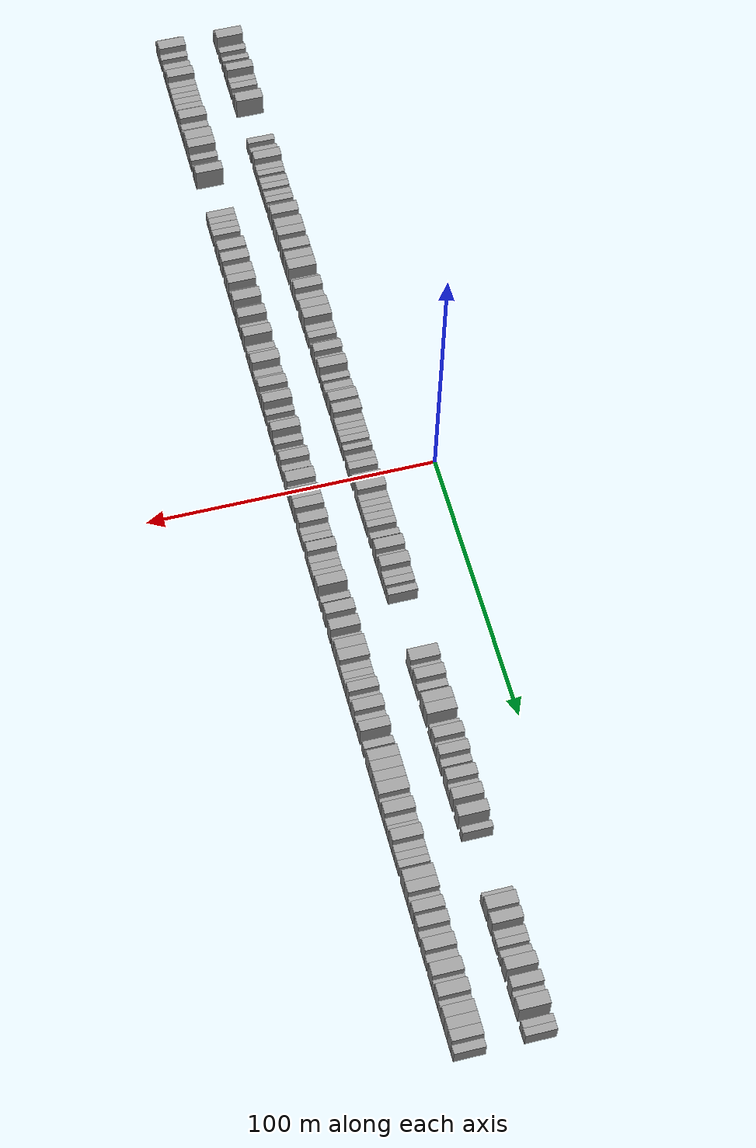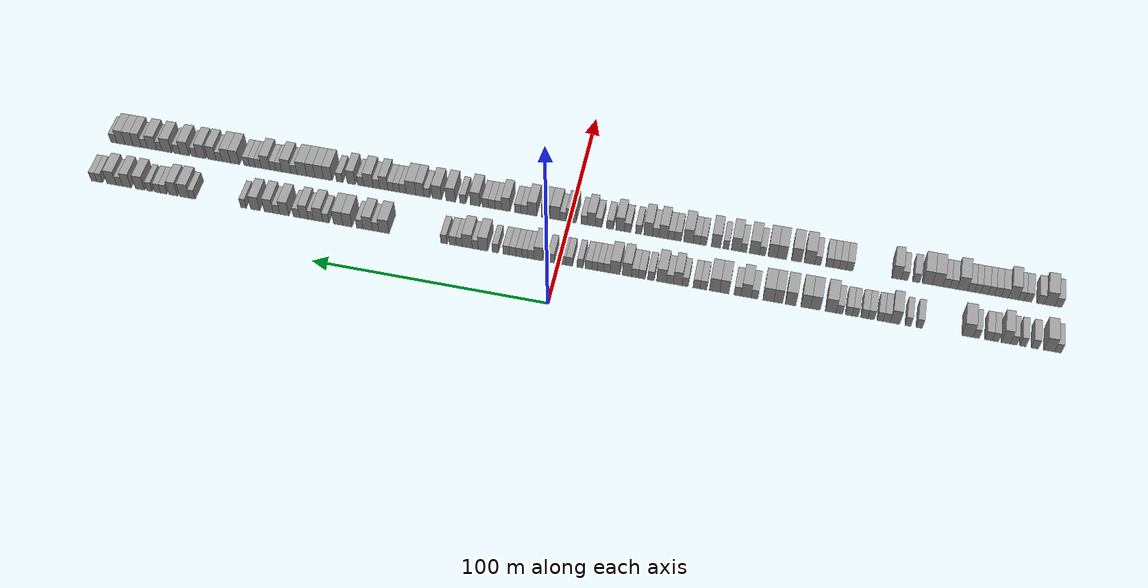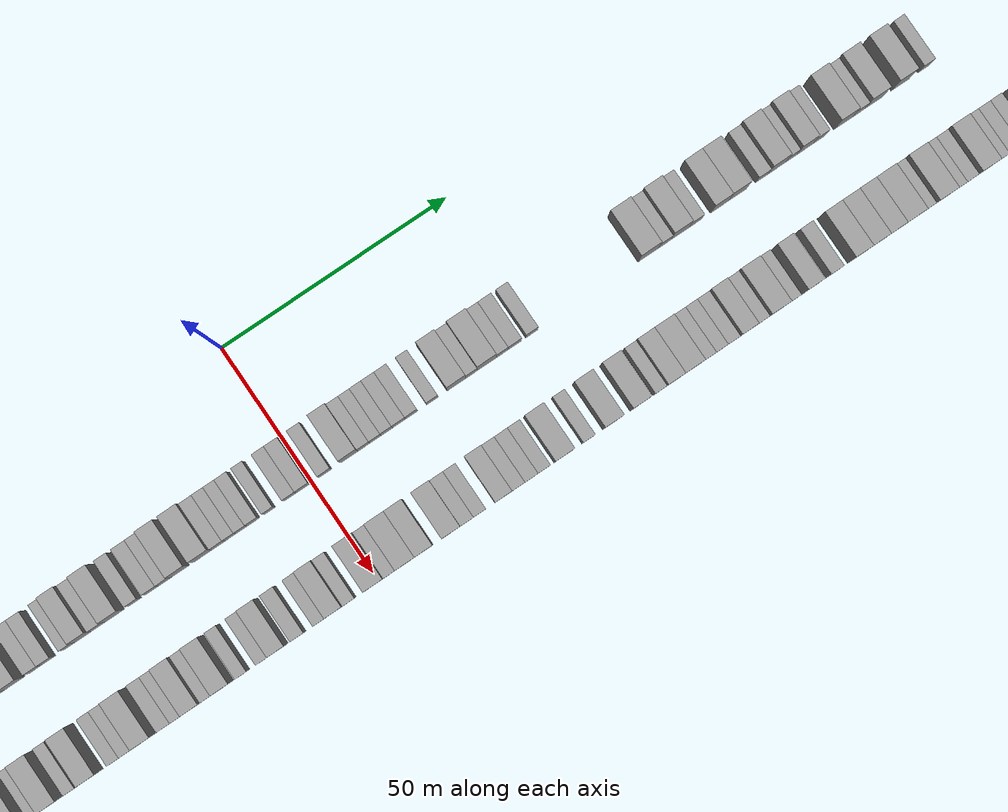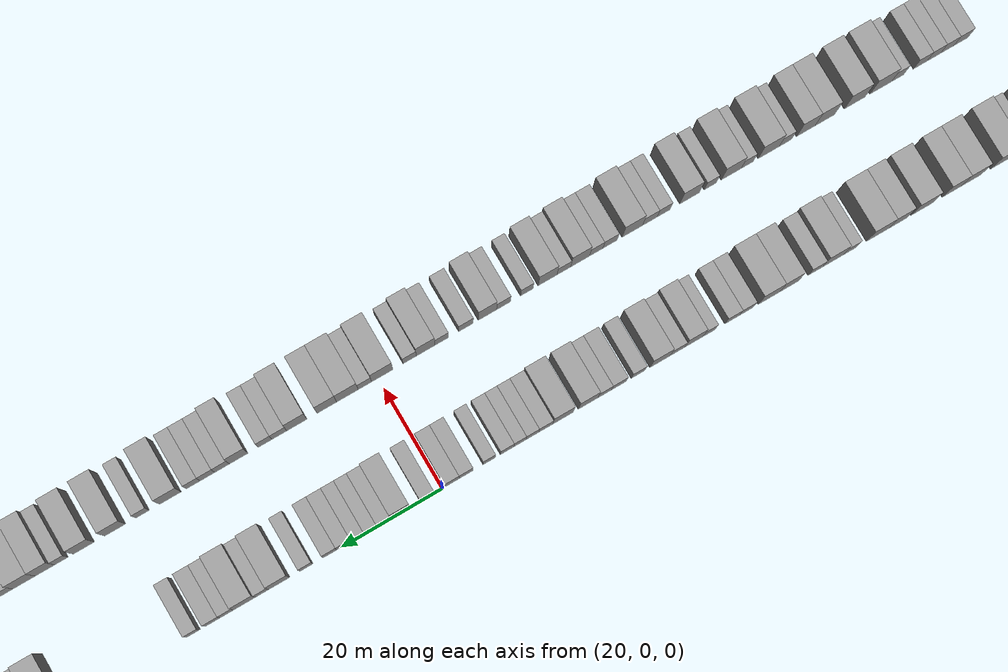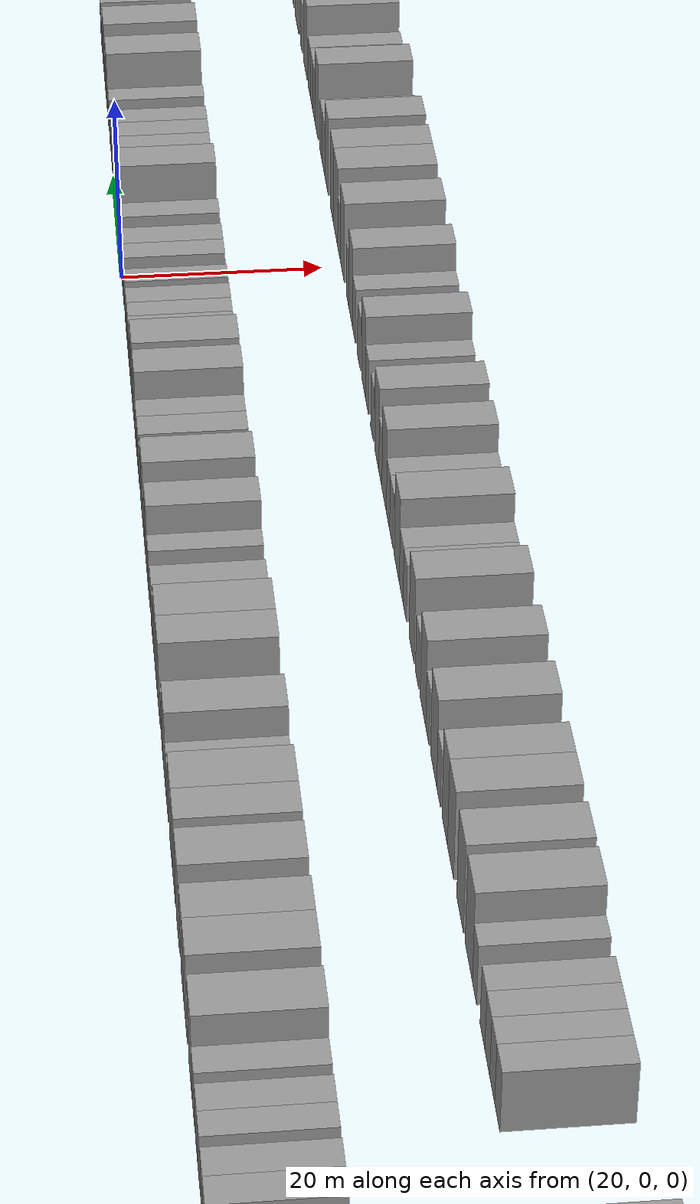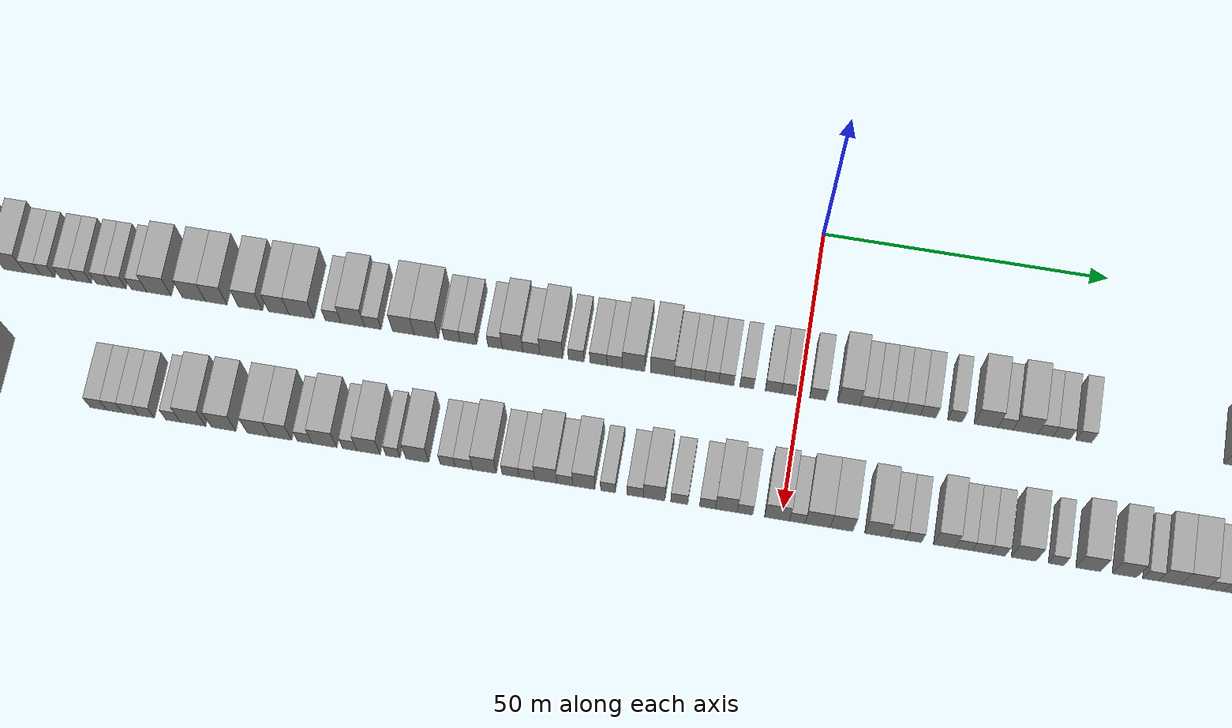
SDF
<sdf version="1.6">
 <world name="default">
  <scene>
   <sky><clouds><speed>12</speed></clouds></sky>
   <ambient>0.4 0.4 0.4 1</ambient>
   <background>0.7 0.7 0.7 1</background>
   <shadows>1</shadows>
  </scene>
  <gravity>0 0 -9.8066</gravity>
  <magnetic_field>6e-06 2.3e-05 -4.2e-05</magnetic_field>
  <physics default="0" name="default_physics" type="ode">
   <ode>
    <solver>
     <type>quick</type>
     <iters>10</iters>
     <sor>1.0</sor>
     <use_dynamic_moi_rescaling>0</use_dynamic_moi_rescaling>
    </solver>
    <constraints>
     <cfm>0</cfm>
     <erp>0.2</erp>
     <contact_max_correcting_vel>100</contact_max_correcting_vel>
     <contact_surface_layer>0.001</contact_surface_layer>
    </constraints>
   </ode>
   <max_step_size>0.004</max_step_size>
   <real_time_factor>1</real_time_factor>
   <real_time_update_rate>250</real_time_update_rate>
  </physics>
  <light name="sun" type="directional">
   <pose>0 0 10 0 0 0</pose>
   <diffuse>0.8 0.8 0.8 1</diffuse>
   <specular>0.2 0.2 0.2 1</specular>
   <attenuation>
    <range>1000</range>
    <constant>0.9</constant>
    <linear>0.01</linear>
    <quadratic>0.001</quadratic>
   </attenuation>
   <direction>-0.5 0.1 -0.9</direction>
  </light>
  <model name="building_1">
   <static>1</static>
   <pose>25.0000 -202.6611 0 0.000000 0.000000 0.000000</pose>
   <link name="link">
    <pose>0 0 3.00 0 0 0</pose>
    <collision name="collision"><geometry><box><size>10.0000 2.6779 6.0000</size></box></geometry></collision>
    <visual name="visual">
     <cast_shadows>0</cast_shadows>
     <geometry><box><size>10.0000 2.6779 6.0000</size></box></geometry>
     <material>
      <script>
       <uri>model://grey_wall/materials/scripts</uri>
       <uri>model://grey_wall/materials/textures</uri>
       <name>vrc/grey_wall</name>
      </script>
     </material>
    </visual>
   </link>
  </model>
  <model name="building_2">
   <static>1</static>
   <pose>25.0000 -199.2296 0 0.000000 0.000000 0.000000</pose>
   <link name="link">
    <pose>0 0 4.50 0 0 0</pose>
    <collision name="collision"><geometry><box><size>10.0000 4.1851 9.0000</size></box></geometry></collision>
    <visual name="visual">
     <cast_shadows>0</cast_shadows>
     <geometry><box><size>10.0000 4.1851 9.0000</size></box></geometry>
     <material>
      <script>
       <uri>model://grey_wall/materials/scripts</uri>
       <uri>model://grey_wall/materials/textures</uri>
       <name>vrc/grey_wall</name>
      </script>
     </material>
    </visual>
   </link>
  </model>
  <model name="building_3">
   <static>1</static>
   <pose>25.0000 -193.6957 0 0.000000 0.000000 0.000000</pose>
   <link name="link">
    <pose>0 0 3.00 0 0 0</pose>
    <collision name="collision"><geometry><box><size>10.0000 2.8827 6.0000</size></box></geometry></collision>
    <visual name="visual">
     <cast_shadows>0</cast_shadows>
     <geometry><box><size>10.0000 2.8827 6.0000</size></box></geometry>
     <material>
      <script>
       <uri>model://grey_wall/materials/scripts</uri>
       <uri>model://grey_wall/materials/textures</uri>
       <name>vrc/grey_wall</name>
      </script>
     </material>
    </visual>
   </link>
  </model>
  <model name="building_4">
   <static>1</static>
   <pose>25.0000 -189.0134 0 0.000000 0.000000 0.000000</pose>
   <link name="link">
    <pose>0 0 3.00 0 0 0</pose>
    <collision name="collision"><geometry><box><size>10.0000 2.4819 6.0000</size></box></geometry></collision>
    <visual name="visual">
     <cast_shadows>0</cast_shadows>
     <geometry><box><size>10.0000 2.4819 6.0000</size></box></geometry>
     <material>
      <script>
       <uri>model://grey_wall/materials/scripts</uri>
       <uri>model://grey_wall/materials/textures</uri>
       <name>vrc/grey_wall</name>
      </script>
     </material>
    </visual>
   </link>
  </model>
  <model name="building_5">
   <static>1</static>
   <pose>25.0000 -185.4390 0 0.000000 0.000000 0.000000</pose>
   <link name="link">
    <pose>0 0 3.00 0 0 0</pose>
    <collision name="collision"><geometry><box><size>10.0000 2.6669 6.0000</size></box></geometry></collision>
    <visual name="visual">
     <cast_shadows>0</cast_shadows>
     <geometry><box><size>10.0000 2.6669 6.0000</size></box></geometry>
     <material>
      <script>
       <uri>model://grey_wall/materials/scripts</uri>
       <uri>model://grey_wall/materials/textures</uri>
       <name>vrc/grey_wall</name>
      </script>
     </material>
    </visual>
   </link>
  </model>
  <model name="building_6">
   <static>1</static>
   <pose>25.0000 -182.3027 0 0.000000 0.000000 0.000000</pose>
   <link name="link">
    <pose>0 0 4.50 0 0 0</pose>
    <collision name="collision"><geometry><box><size>10.0000 3.6058 9.0000</size></box></geometry></collision>
    <visual name="visual">
     <cast_shadows>0</cast_shadows>
     <geometry><box><size>10.0000 3.6058 9.0000</size></box></geometry>
     <material>
      <script>
       <uri>model://grey_wall/materials/scripts</uri>
       <uri>model://grey_wall/materials/textures</uri>
       <name>vrc/grey_wall</name>
      </script>
     </material>
    </visual>
   </link>
  </model>
  <model name="building_7">
   <static>1</static>
   <pose>25.0000 -178.2073 0 0.000000 0.000000 0.000000</pose>
   <link name="link">
    <pose>0 0 3.00 0 0 0</pose>
    <collision name="collision"><geometry><box><size>10.0000 2.5851 6.0000</size></box></geometry></collision>
    <visual name="visual">
     <cast_shadows>0</cast_shadows>
     <geometry><box><size>10.0000 2.5851 6.0000</size></box></geometry>
     <material>
      <script>
       <uri>model://grey_wall/materials/scripts</uri>
       <uri>model://grey_wall/materials/textures</uri>
       <name>vrc/grey_wall</name>
      </script>
     </material>
    </visual>
   </link>
  </model>
  <model name="building_8">
   <static>1</static>
   <pose>25.0000 -175.4438 0 0.000000 0.000000 0.000000</pose>
   <link name="link">
    <pose>0 0 3.00 0 0 0</pose>
    <collision name="collision"><geometry><box><size>10.0000 2.9420 6.0000</size></box></geometry></collision>
    <visual name="visual">
     <cast_shadows>0</cast_shadows>
     <geometry><box><size>10.0000 2.9420 6.0000</size></box></geometry>
     <material>
      <script>
       <uri>model://grey_wall/materials/scripts</uri>
       <uri>model://grey_wall/materials/textures</uri>
       <name>vrc/grey_wall</name>
      </script>
     </material>
    </visual>
   </link>
  </model>
  <model name="building_9">
   <static>1</static>
   <pose>25.0000 -170.6992 0 0.000000 0.000000 0.000000</pose>
   <link name="link">
    <pose>0 0 3.00 0 0 0</pose>
    <collision name="collision"><geometry><box><size>10.0000 2.5470 6.0000</size></box></geometry></collision>
    <visual name="visual">
     <cast_shadows>0</cast_shadows>
     <geometry><box><size>10.0000 2.5470 6.0000</size></box></geometry>
     <material>
      <script>
       <uri>model://grey_wall/materials/scripts</uri>
       <uri>model://grey_wall/materials/textures</uri>
       <name>vrc/grey_wall</name>
      </script>
     </material>
    </visual>
   </link>
  </model>
  <model name="building_10">
   <static>1</static>
   <pose>25.0000 -167.2199 0 0.000000 0.000000 0.000000</pose>
   <link name="link">
    <pose>0 0 4.50 0 0 0</pose>
    <collision name="collision"><geometry><box><size>10.0000 4.4116 9.0000</size></box></geometry></collision>
    <visual name="visual">
     <cast_shadows>0</cast_shadows>
     <geometry><box><size>10.0000 4.4116 9.0000</size></box></geometry>
     <material>
      <script>
       <uri>model://grey_wall/materials/scripts</uri>
       <uri>model://grey_wall/materials/textures</uri>
       <name>vrc/grey_wall</name>
      </script>
     </material>
    </visual>
   </link>
  </model>
  <model name="building_11">
   <static>1</static>
   <pose>25.0000 -148.1535 0 0.000000 0.000000 0.000000</pose>
   <link name="link">
    <pose>0 0 3.00 0 0 0</pose>
    <collision name="collision"><geometry><box><size>10.0000 2.5738 6.0000</size></box></geometry></collision>
    <visual name="visual">
     <cast_shadows>0</cast_shadows>
     <geometry><box><size>10.0000 2.5738 6.0000</size></box></geometry>
     <material>
      <script>
       <uri>model://grey_wall/materials/scripts</uri>
       <uri>model://grey_wall/materials/textures</uri>
       <name>vrc/grey_wall</name>
      </script>
     </material>
    </visual>
   </link>
  </model>
  <model name="building_12">
   <static>1</static>
   <pose>25.0000 -143.6613 0 0.000000 0.000000 0.000000</pose>
   <link name="link">
    <pose>0 0 3.00 0 0 0</pose>
    <collision name="collision"><geometry><box><size>10.0000 2.4105 6.0000</size></box></geometry></collision>
    <visual name="visual">
     <cast_shadows>0</cast_shadows>
     <geometry><box><size>10.0000 2.4105 6.0000</size></box></geometry>
     <material>
      <script>
       <uri>model://grey_wall/materials/scripts</uri>
       <uri>model://grey_wall/materials/textures</uri>
       <name>vrc/grey_wall</name>
      </script>
     </material>
    </visual>
   </link>
  </model>
  <model name="building_13">
   <static>1</static>
   <pose>25.0000 -138.5214 0 0.000000 0.000000 0.000000</pose>
   <link name="link">
    <pose>0 0 4.50 0 0 0</pose>
    <collision name="collision"><geometry><box><size>10.0000 3.8694 9.0000</size></box></geometry></collision>
    <visual name="visual">
     <cast_shadows>0</cast_shadows>
     <geometry><box><size>10.0000 3.8694 9.0000</size></box></geometry>
     <material>
      <script>
       <uri>model://grey_wall/materials/scripts</uri>
       <uri>model://grey_wall/materials/textures</uri>
       <name>vrc/grey_wall</name>
      </script>
     </material>
    </visual>
   </link>
  </model>
  <model name="building_14">
   <static>1</static>
   <pose>25.0000 -135.1633 0 0.000000 0.000000 0.000000</pose>
   <link name="link">
    <pose>0 0 3.00 0 0 0</pose>
    <collision name="collision"><geometry><box><size>10.0000 2.8466 6.0000</size></box></geometry></collision>
    <visual name="visual">
     <cast_shadows>0</cast_shadows>
     <geometry><box><size>10.0000 2.8466 6.0000</size></box></geometry>
     <material>
      <script>
       <uri>model://grey_wall/materials/scripts</uri>
       <uri>model://grey_wall/materials/textures</uri>
       <name>vrc/grey_wall</name>
      </script>
     </material>
    </visual>
   </link>
  </model>
  <model name="building_15">
   <static>1</static>
   <pose>25.0000 -132.5168 0 0.000000 0.000000 0.000000</pose>
   <link name="link">
    <pose>0 0 3.00 0 0 0</pose>
    <collision name="collision"><geometry><box><size>10.0000 2.4464 6.0000</size></box></geometry></collision>
    <visual name="visual">
     <cast_shadows>0</cast_shadows>
     <geometry><box><size>10.0000 2.4464 6.0000</size></box></geometry>
     <material>
      <script>
       <uri>model://grey_wall/materials/scripts</uri>
       <uri>model://grey_wall/materials/textures</uri>
       <name>vrc/grey_wall</name>
      </script>
     </material>
    </visual>
   </link>
  </model>
  <model name="building_16">
   <static>1</static>
   <pose>25.0000 -128.9212 0 0.000000 0.000000 0.000000</pose>
   <link name="link">
    <pose>0 0 3.00 0 0 0</pose>
    <collision name="collision"><geometry><box><size>10.0000 2.7448 6.0000</size></box></geometry></collision>
    <visual name="visual">
     <cast_shadows>0</cast_shadows>
     <geometry><box><size>10.0000 2.7448 6.0000</size></box></geometry>
     <material>
      <script>
       <uri>model://grey_wall/materials/scripts</uri>
       <uri>model://grey_wall/materials/textures</uri>
       <name>vrc/grey_wall</name>
      </script>
     </material>
    </visual>
   </link>
  </model>
  <model name="building_17">
   <static>1</static>
   <pose>25.0000 -126.1748 0 0.000000 0.000000 0.000000</pose>
   <link name="link">
    <pose>0 0 3.00 0 0 0</pose>
    <collision name="collision"><geometry><box><size>10.0000 2.7481 6.0000</size></box></geometry></collision>
    <visual name="visual">
     <cast_shadows>0</cast_shadows>
     <geometry><box><size>10.0000 2.7481 6.0000</size></box></geometry>
     <material>
      <script>
       <uri>model://grey_wall/materials/scripts</uri>
       <uri>model://grey_wall/materials/textures</uri>
       <name>vrc/grey_wall</name>
      </script>
     </material>
    </visual>
   </link>
  </model>
  <model name="building_18">
   <static>1</static>
   <pose>25.0000 -122.5415 0 0.000000 0.000000 0.000000</pose>
   <link name="link">
    <pose>0 0 3.00 0 0 0</pose>
    <collision name="collision"><geometry><box><size>10.0000 2.5185 6.0000</size></box></geometry></collision>
    <visual name="visual">
     <cast_shadows>0</cast_shadows>
     <geometry><box><size>10.0000 2.5185 6.0000</size></box></geometry>
     <material>
      <script>
       <uri>model://grey_wall/materials/scripts</uri>
       <uri>model://grey_wall/materials/textures</uri>
       <name>vrc/grey_wall</name>
      </script>
     </material>
    </visual>
   </link>
  </model>
  <model name="building_19">
   <static>1</static>
   <pose>25.0000 -119.9310 0 0.000000 0.000000 0.000000</pose>
   <link name="link">
    <pose>0 0 3.00 0 0 0</pose>
    <collision name="collision"><geometry><box><size>10.0000 2.7025 6.0000</size></box></geometry></collision>
    <visual name="visual">
     <cast_shadows>0</cast_shadows>
     <geometry><box><size>10.0000 2.7025 6.0000</size></box></geometry>
     <material>
      <script>
       <uri>model://grey_wall/materials/scripts</uri>
       <uri>model://grey_wall/materials/textures</uri>
       <name>vrc/grey_wall</name>
      </script>
     </material>
    </visual>
   </link>
  </model>
  <model name="building_20">
   <static>1</static>
   <pose>25.0000 -116.2105 0 0.000000 0.000000 0.000000</pose>
   <link name="link">
    <pose>0 0 3.00 0 0 0</pose>
    <collision name="collision"><geometry><box><size>10.0000 2.7385 6.0000</size></box></geometry></collision>
    <visual name="visual">
     <cast_shadows>0</cast_shadows>
     <geometry><box><size>10.0000 2.7385 6.0000</size></box></geometry>
     <material>
      <script>
       <uri>model://grey_wall/materials/scripts</uri>
       <uri>model://grey_wall/materials/textures</uri>
       <name>vrc/grey_wall</name>
      </script>
     </material>
    </visual>
   </link>
  </model>
  <model name="building_21">
   <static>1</static>
   <pose>25.0000 -112.6625 0 0.000000 0.000000 0.000000</pose>
   <link name="link">
    <pose>0 0 4.50 0 0 0</pose>
    <collision name="collision"><geometry><box><size>10.0000 4.3575 9.0000</size></box></geometry></collision>
    <visual name="visual">
     <cast_shadows>0</cast_shadows>
     <geometry><box><size>10.0000 4.3575 9.0000</size></box></geometry>
     <material>
      <script>
       <uri>model://grey_wall/materials/scripts</uri>
       <uri>model://grey_wall/materials/textures</uri>
       <name>vrc/grey_wall</name>
      </script>
     </material>
    </visual>
   </link>
  </model>
  <model name="building_22">
   <static>1</static>
   <pose>25.0000 -106.4396 0 0.000000 0.000000 0.000000</pose>
   <link name="link">
    <pose>0 0 4.50 0 0 0</pose>
    <collision name="collision"><geometry><box><size>10.0000 4.0883 9.0000</size></box></geometry></collision>
    <visual name="visual">
     <cast_shadows>0</cast_shadows>
     <geometry><box><size>10.0000 4.0883 9.0000</size></box></geometry>
     <material>
      <script>
       <uri>model://grey_wall/materials/scripts</uri>
       <uri>model://grey_wall/materials/textures</uri>
       <name>vrc/grey_wall</name>
      </script>
     </material>
    </visual>
   </link>
  </model>
  <model name="building_23">
   <static>1</static>
   <pose>25.0000 -102.4814 0 0.000000 0.000000 0.000000</pose>
   <link name="link">
    <pose>0 0 4.50 0 0 0</pose>
    <collision name="collision"><geometry><box><size>10.0000 3.8283 9.0000</size></box></geometry></collision>
    <visual name="visual">
     <cast_shadows>0</cast_shadows>
     <geometry><box><size>10.0000 3.8283 9.0000</size></box></geometry>
     <material>
      <script>
       <uri>model://grey_wall/materials/scripts</uri>
       <uri>model://grey_wall/materials/textures</uri>
       <name>vrc/grey_wall</name>
      </script>
     </material>
    </visual>
   </link>
  </model>
  <model name="building_24">
   <static>1</static>
   <pose>25.0000 -96.3941 0 0.000000 0.000000 0.000000</pose>
   <link name="link">
    <pose>0 0 4.50 0 0 0</pose>
    <collision name="collision"><geometry><box><size>10.0000 4.3463 9.0000</size></box></geometry></collision>
    <visual name="visual">
     <cast_shadows>0</cast_shadows>
     <geometry><box><size>10.0000 4.3463 9.0000</size></box></geometry>
     <material>
      <script>
       <uri>model://grey_wall/materials/scripts</uri>
       <uri>model://grey_wall/materials/textures</uri>
       <name>vrc/grey_wall</name>
      </script>
     </material>
    </visual>
   </link>
  </model>
  <model name="building_25">
   <static>1</static>
   <pose>25.0000 -91.3771 0 0.000000 0.000000 0.000000</pose>
   <link name="link">
    <pose>0 0 4.50 0 0 0</pose>
    <collision name="collision"><geometry><box><size>10.0000 3.6876 9.0000</size></box></geometry></collision>
    <visual name="visual">
     <cast_shadows>0</cast_shadows>
     <geometry><box><size>10.0000 3.6876 9.0000</size></box></geometry>
     <material>
      <script>
       <uri>model://grey_wall/materials/scripts</uri>
       <uri>model://grey_wall/materials/textures</uri>
       <name>vrc/grey_wall</name>
      </script>
     </material>
    </visual>
   </link>
  </model>
  <model name="building_26">
   <static>1</static>
   <pose>25.0000 -87.3219 0 0.000000 0.000000 0.000000</pose>
   <link name="link">
    <pose>0 0 4.50 0 0 0</pose>
    <collision name="collision"><geometry><box><size>10.0000 4.4229 9.0000</size></box></geometry></collision>
    <visual name="visual">
     <cast_shadows>0</cast_shadows>
     <geometry><box><size>10.0000 4.4229 9.0000</size></box></geometry>
     <material>
      <script>
       <uri>model://grey_wall/materials/scripts</uri>
       <uri>model://grey_wall/materials/textures</uri>
       <name>vrc/grey_wall</name>
      </script>
     </material>
    </visual>
   </link>
  </model>
  <model name="building_27">
   <static>1</static>
   <pose>25.0000 -81.7084 0 0.000000 0.000000 0.000000</pose>
   <link name="link">
    <pose>0 0 3.00 0 0 0</pose>
    <collision name="collision"><geometry><box><size>10.0000 2.8041 6.0000</size></box></geometry></collision>
    <visual name="visual">
     <cast_shadows>0</cast_shadows>
     <geometry><box><size>10.0000 2.8041 6.0000</size></box></geometry>
     <material>
      <script>
       <uri>model://grey_wall/materials/scripts</uri>
       <uri>model://grey_wall/materials/textures</uri>
       <name>vrc/grey_wall</name>
      </script>
     </material>
    </visual>
   </link>
  </model>
  <model name="building_28">
   <static>1</static>
   <pose>25.0000 -78.2339 0 0.000000 0.000000 0.000000</pose>
   <link name="link">
    <pose>0 0 4.50 0 0 0</pose>
    <collision name="collision"><geometry><box><size>10.0000 4.1448 9.0000</size></box></geometry></collision>
    <visual name="visual">
     <cast_shadows>0</cast_shadows>
     <geometry><box><size>10.0000 4.1448 9.0000</size></box></geometry>
     <material>
      <script>
       <uri>model://grey_wall/materials/scripts</uri>
       <uri>model://grey_wall/materials/textures</uri>
       <name>vrc/grey_wall</name>
      </script>
     </material>
    </visual>
   </link>
  </model>
  <model name="building_29">
   <static>1</static>
   <pose>25.0000 -74.7039 0 0.000000 0.000000 0.000000</pose>
   <link name="link">
    <pose>0 0 3.00 0 0 0</pose>
    <collision name="collision"><geometry><box><size>10.0000 2.9154 6.0000</size></box></geometry></collision>
    <visual name="visual">
     <cast_shadows>0</cast_shadows>
     <geometry><box><size>10.0000 2.9154 6.0000</size></box></geometry>
     <material>
      <script>
       <uri>model://grey_wall/materials/scripts</uri>
       <uri>model://grey_wall/materials/textures</uri>
       <name>vrc/grey_wall</name>
      </script>
     </material>
    </visual>
   </link>
  </model>
  <model name="building_30">
   <static>1</static>
   <pose>25.0000 -69.3345 0 0.000000 0.000000 0.000000</pose>
   <link name="link">
    <pose>0 0 4.50 0 0 0</pose>
    <collision name="collision"><geometry><box><size>10.0000 3.8234 9.0000</size></box></geometry></collision>
    <visual name="visual">
     <cast_shadows>0</cast_shadows>
     <geometry><box><size>10.0000 3.8234 9.0000</size></box></geometry>
     <material>
      <script>
       <uri>model://grey_wall/materials/scripts</uri>
       <uri>model://grey_wall/materials/textures</uri>
       <name>vrc/grey_wall</name>
      </script>
     </material>
    </visual>
   </link>
  </model>
  <model name="building_31">
   <static>1</static>
   <pose>25.0000 -65.2786 0 0.000000 0.000000 0.000000</pose>
   <link name="link">
    <pose>0 0 4.50 0 0 0</pose>
    <collision name="collision"><geometry><box><size>10.0000 4.2884 9.0000</size></box></geometry></collision>
    <visual name="visual">
     <cast_shadows>0</cast_shadows>
     <geometry><box><size>10.0000 4.2884 9.0000</size></box></geometry>
     <material>
      <script>
       <uri>model://grey_wall/materials/scripts</uri>
       <uri>model://grey_wall/materials/textures</uri>
       <name>vrc/grey_wall</name>
      </script>
     </material>
    </visual>
   </link>
  </model>
  <model name="building_32">
   <static>1</static>
   <pose>25.0000 -60.7182 0 0.000000 0.000000 0.000000</pose>
   <link name="link">
    <pose>0 0 3.00 0 0 0</pose>
    <collision name="collision"><geometry><box><size>10.0000 2.8323 6.0000</size></box></geometry></collision>
    <visual name="visual">
     <cast_shadows>0</cast_shadows>
     <geometry><box><size>10.0000 2.8323 6.0000</size></box></geometry>
     <material>
      <script>
       <uri>model://grey_wall/materials/scripts</uri>
       <uri>model://grey_wall/materials/textures</uri>
       <name>vrc/grey_wall</name>
      </script>
     </material>
    </visual>
   </link>
  </model>
  <model name="building_33">
   <static>1</static>
   <pose>25.0000 -57.8612 0 0.000000 0.000000 0.000000</pose>
   <link name="link">
    <pose>0 0 3.00 0 0 0</pose>
    <collision name="collision"><geometry><box><size>10.0000 2.8819 6.0000</size></box></geometry></collision>
    <visual name="visual">
     <cast_shadows>0</cast_shadows>
     <geometry><box><size>10.0000 2.8819 6.0000</size></box></geometry>
     <material>
      <script>
       <uri>model://grey_wall/materials/scripts</uri>
       <uri>model://grey_wall/materials/textures</uri>
       <name>vrc/grey_wall</name>
      </script>
     </material>
    </visual>
   </link>
  </model>
  <model name="building_34">
   <static>1</static>
   <pose>25.0000 -53.1745 0 0.000000 0.000000 0.000000</pose>
   <link name="link">
    <pose>0 0 3.00 0 0 0</pose>
    <collision name="collision"><geometry><box><size>10.0000 2.4914 6.0000</size></box></geometry></collision>
    <visual name="visual">
     <cast_shadows>0</cast_shadows>
     <geometry><box><size>10.0000 2.4914 6.0000</size></box></geometry>
     <material>
      <script>
       <uri>model://grey_wall/materials/scripts</uri>
       <uri>model://grey_wall/materials/textures</uri>
       <name>vrc/grey_wall</name>
      </script>
     </material>
    </visual>
   </link>
  </model>
  <model name="building_35">
   <static>1</static>
   <pose>25.0000 -50.1071 0 0.000000 0.000000 0.000000</pose>
   <link name="link">
    <pose>0 0 4.50 0 0 0</pose>
    <collision name="collision"><geometry><box><size>10.0000 3.6433 9.0000</size></box></geometry></collision>
    <visual name="visual">
     <cast_shadows>0</cast_shadows>
     <geometry><box><size>10.0000 3.6433 9.0000</size></box></geometry>
     <material>
      <script>
       <uri>model://grey_wall/materials/scripts</uri>
       <uri>model://grey_wall/materials/textures</uri>
       <name>vrc/grey_wall</name>
      </script>
     </material>
    </visual>
   </link>
  </model>
  <model name="building_36">
   <static>1</static>
   <pose>25.0000 -46.8084 0 0.000000 0.000000 0.000000</pose>
   <link name="link">
    <pose>0 0 3.00 0 0 0</pose>
    <collision name="collision"><geometry><box><size>10.0000 2.9542 6.0000</size></box></geometry></collision>
    <visual name="visual">
     <cast_shadows>0</cast_shadows>
     <geometry><box><size>10.0000 2.9542 6.0000</size></box></geometry>
     <material>
      <script>
       <uri>model://grey_wall/materials/scripts</uri>
       <uri>model://grey_wall/materials/textures</uri>
       <name>vrc/grey_wall</name>
      </script>
     </material>
    </visual>
   </link>
  </model>
  <model name="building_37">
   <static>1</static>
   <pose>25.0000 -43.3274 0 0.000000 0.000000 0.000000</pose>
   <link name="link">
    <pose>0 0 4.50 0 0 0</pose>
    <collision name="collision"><geometry><box><size>10.0000 4.0077 9.0000</size></box></geometry></collision>
    <visual name="visual">
     <cast_shadows>0</cast_shadows>
     <geometry><box><size>10.0000 4.0077 9.0000</size></box></geometry>
     <material>
      <script>
       <uri>model://grey_wall/materials/scripts</uri>
       <uri>model://grey_wall/materials/textures</uri>
       <name>vrc/grey_wall</name>
      </script>
     </material>
    </visual>
   </link>
  </model>
  <model name="building_38">
   <static>1</static>
   <pose>25.0000 -38.9517 0 0.000000 0.000000 0.000000</pose>
   <link name="link">
    <pose>0 0 3.00 0 0 0</pose>
    <collision name="collision"><geometry><box><size>10.0000 2.7437 6.0000</size></box></geometry></collision>
    <visual name="visual">
     <cast_shadows>0</cast_shadows>
     <geometry><box><size>10.0000 2.7437 6.0000</size></box></geometry>
     <material>
      <script>
       <uri>model://grey_wall/materials/scripts</uri>
       <uri>model://grey_wall/materials/textures</uri>
       <name>vrc/grey_wall</name>
      </script>
     </material>
    </visual>
   </link>
  </model>
  <model name="building_39">
   <static>1</static>
   <pose>25.0000 -35.0839 0 0.000000 0.000000 0.000000</pose>
   <link name="link">
    <pose>0 0 3.00 0 0 0</pose>
    <collision name="collision"><geometry><box><size>10.0000 2.9920 6.0000</size></box></geometry></collision>
    <visual name="visual">
     <cast_shadows>0</cast_shadows>
     <geometry><box><size>10.0000 2.9920 6.0000</size></box></geometry>
     <material>
      <script>
       <uri>model://grey_wall/materials/scripts</uri>
       <uri>model://grey_wall/materials/textures</uri>
       <name>vrc/grey_wall</name>
      </script>
     </material>
    </visual>
   </link>
  </model>
  <model name="building_40">
   <static>1</static>
   <pose>25.0000 -32.2268 0 0.000000 0.000000 0.000000</pose>
   <link name="link">
    <pose>0 0 3.00 0 0 0</pose>
    <collision name="collision"><geometry><box><size>10.0000 2.7221 6.0000</size></box></geometry></collision>
    <visual name="visual">
     <cast_shadows>0</cast_shadows>
     <geometry><box><size>10.0000 2.7221 6.0000</size></box></geometry>
     <material>
      <script>
       <uri>model://grey_wall/materials/scripts</uri>
       <uri>model://grey_wall/materials/textures</uri>
       <name>vrc/grey_wall</name>
      </script>
     </material>
    </visual>
   </link>
  </model>
  <model name="building_41">
   <static>1</static>
   <pose>25.0000 -28.9342 0 0.000000 0.000000 0.000000</pose>
   <link name="link">
    <pose>0 0 4.50 0 0 0</pose>
    <collision name="collision"><geometry><box><size>10.0000 3.8631 9.0000</size></box></geometry></collision>
    <visual name="visual">
     <cast_shadows>0</cast_shadows>
     <geometry><box><size>10.0000 3.8631 9.0000</size></box></geometry>
     <material>
      <script>
       <uri>model://grey_wall/materials/scripts</uri>
       <uri>model://grey_wall/materials/textures</uri>
       <name>vrc/grey_wall</name>
      </script>
     </material>
    </visual>
   </link>
  </model>
  <model name="building_42">
   <static>1</static>
   <pose>25.0000 -23.9448 0 0.000000 0.000000 0.000000</pose>
   <link name="link">
    <pose>0 0 4.50 0 0 0</pose>
    <collision name="collision"><geometry><box><size>10.0000 4.1158 9.0000</size></box></geometry></collision>
    <visual name="visual">
     <cast_shadows>0</cast_shadows>
     <geometry><box><size>10.0000 4.1158 9.0000</size></box></geometry>
     <material>
      <script>
       <uri>model://grey_wall/materials/scripts</uri>
       <uri>model://grey_wall/materials/textures</uri>
       <name>vrc/grey_wall</name>
      </script>
     </material>
    </visual>
   </link>
  </model>
  <model name="building_43">
   <static>1</static>
   <pose>25.0000 -20.4811 0 0.000000 0.000000 0.000000</pose>
   <link name="link">
    <pose>0 0 3.00 0 0 0</pose>
    <collision name="collision"><geometry><box><size>10.0000 2.8116 6.0000</size></box></geometry></collision>
    <visual name="visual">
     <cast_shadows>0</cast_shadows>
     <geometry><box><size>10.0000 2.8116 6.0000</size></box></geometry>
     <material>
      <script>
       <uri>model://grey_wall/materials/scripts</uri>
       <uri>model://grey_wall/materials/textures</uri>
       <name>vrc/grey_wall</name>
      </script>
     </material>
    </visual>
   </link>
  </model>
  <model name="building_44">
   <static>1</static>
   <pose>25.0000 -17.8155 0 0.000000 0.000000 0.000000</pose>
   <link name="link">
    <pose>0 0 3.00 0 0 0</pose>
    <collision name="collision"><geometry><box><size>10.0000 2.5195 6.0000</size></box></geometry></collision>
    <visual name="visual">
     <cast_shadows>0</cast_shadows>
     <geometry><box><size>10.0000 2.5195 6.0000</size></box></geometry>
     <material>
      <script>
       <uri>model://grey_wall/materials/scripts</uri>
       <uri>model://grey_wall/materials/textures</uri>
       <name>vrc/grey_wall</name>
      </script>
     </material>
    </visual>
   </link>
  </model>
  <model name="building_45">
   <static>1</static>
   <pose>25.0000 -15.3467 0 0.000000 0.000000 0.000000</pose>
   <link name="link">
    <pose>0 0 3.00 0 0 0</pose>
    <collision name="collision"><geometry><box><size>10.0000 2.4181 6.0000</size></box></geometry></collision>
    <visual name="visual">
     <cast_shadows>0</cast_shadows>
     <geometry><box><size>10.0000 2.4181 6.0000</size></box></geometry>
     <material>
      <script>
       <uri>model://grey_wall/materials/scripts</uri>
       <uri>model://grey_wall/materials/textures</uri>
       <name>vrc/grey_wall</name>
      </script>
     </material>
    </visual>
   </link>
  </model>
  <model name="building_46">
   <static>1</static>
   <pose>25.0000 -12.8056 0 0.000000 0.000000 0.000000</pose>
   <link name="link">
    <pose>0 0 3.00 0 0 0</pose>
    <collision name="collision"><geometry><box><size>10.0000 2.6641 6.0000</size></box></geometry></collision>
    <visual name="visual">
     <cast_shadows>0</cast_shadows>
     <geometry><box><size>10.0000 2.6641 6.0000</size></box></geometry>
     <material>
      <script>
       <uri>model://grey_wall/materials/scripts</uri>
       <uri>model://grey_wall/materials/textures</uri>
       <name>vrc/grey_wall</name>
      </script>
     </material>
    </visual>
   </link>
  </model>
  <model name="building_47">
   <static>1</static>
   <pose>25.0000 -9.2607 0 0.000000 0.000000 0.000000</pose>
   <link name="link">
    <pose>0 0 3.00 0 0 0</pose>
    <collision name="collision"><geometry><box><size>10.0000 2.4256 6.0000</size></box></geometry></collision>
    <visual name="visual">
     <cast_shadows>0</cast_shadows>
     <geometry><box><size>10.0000 2.4256 6.0000</size></box></geometry>
     <material>
      <script>
       <uri>model://grey_wall/materials/scripts</uri>
       <uri>model://grey_wall/materials/textures</uri>
       <name>vrc/grey_wall</name>
      </script>
     </material>
    </visual>
   </link>
  </model>
  <model name="building_48">
   <static>1</static>
   <pose>25.0000 -4.6812 0 0.000000 0.000000 0.000000</pose>
   <link name="link">
    <pose>0 0 3.00 0 0 0</pose>
    <collision name="collision"><geometry><box><size>10.0000 2.7335 6.0000</size></box></geometry></collision>
    <visual name="visual">
     <cast_shadows>0</cast_shadows>
     <geometry><box><size>10.0000 2.7335 6.0000</size></box></geometry>
     <material>
      <script>
       <uri>model://grey_wall/materials/scripts</uri>
       <uri>model://grey_wall/materials/textures</uri>
       <name>vrc/grey_wall</name>
      </script>
     </material>
    </visual>
   </link>
  </model>
  <model name="building_49">
   <static>1</static>
   <pose>25.0000 -1.8331 0 0.000000 0.000000 0.000000</pose>
   <link name="link">
    <pose>0 0 3.00 0 0 0</pose>
    <collision name="collision"><geometry><box><size>10.0000 2.9627 6.0000</size></box></geometry></collision>
    <visual name="visual">
     <cast_shadows>0</cast_shadows>
     <geometry><box><size>10.0000 2.9627 6.0000</size></box></geometry>
     <material>
      <script>
       <uri>model://grey_wall/materials/scripts</uri>
       <uri>model://grey_wall/materials/textures</uri>
       <name>vrc/grey_wall</name>
      </script>
     </material>
    </visual>
   </link>
  </model>
  <model name="building_50">
   <static>1</static>
   <pose>25.0000 3.0453 0 0.000000 0.000000 0.000000</pose>
   <link name="link">
    <pose>0 0 3.00 0 0 0</pose>
    <collision name="collision"><geometry><box><size>10.0000 2.7942 6.0000</size></box></geometry></collision>
    <visual name="visual">
     <cast_shadows>0</cast_shadows>
     <geometry><box><size>10.0000 2.7942 6.0000</size></box></geometry>
     <material>
      <script>
       <uri>model://grey_wall/materials/scripts</uri>
       <uri>model://grey_wall/materials/textures</uri>
       <name>vrc/grey_wall</name>
      </script>
     </material>
    </visual>
   </link>
  </model>
  <model name="building_51">
   <static>1</static>
   <pose>25.0000 8.3558 0 0.000000 0.000000 0.000000</pose>
   <link name="link">
    <pose>0 0 4.50 0 0 0</pose>
    <collision name="collision"><geometry><box><size>10.0000 3.8267 9.0000</size></box></geometry></collision>
    <visual name="visual">
     <cast_shadows>0</cast_shadows>
     <geometry><box><size>10.0000 3.8267 9.0000</size></box></geometry>
     <material>
      <script>
       <uri>model://grey_wall/materials/scripts</uri>
       <uri>model://grey_wall/materials/textures</uri>
       <name>vrc/grey_wall</name>
      </script>
     </material>
    </visual>
   </link>
  </model>
  <model name="building_52">
   <static>1</static>
   <pose>25.0000 11.5897 0 0.000000 0.000000 0.000000</pose>
   <link name="link">
    <pose>0 0 3.00 0 0 0</pose>
    <collision name="collision"><geometry><box><size>10.0000 2.6410 6.0000</size></box></geometry></collision>
    <visual name="visual">
     <cast_shadows>0</cast_shadows>
     <geometry><box><size>10.0000 2.6410 6.0000</size></box></geometry>
     <material>
      <script>
       <uri>model://grey_wall/materials/scripts</uri>
       <uri>model://grey_wall/materials/textures</uri>
       <name>vrc/grey_wall</name>
      </script>
     </material>
    </visual>
   </link>
  </model>
  <model name="building_53">
   <static>1</static>
   <pose>25.0000 14.1495 0 0.000000 0.000000 0.000000</pose>
   <link name="link">
    <pose>0 0 3.00 0 0 0</pose>
    <collision name="collision"><geometry><box><size>10.0000 2.4786 6.0000</size></box></geometry></collision>
    <visual name="visual">
     <cast_shadows>0</cast_shadows>
     <geometry><box><size>10.0000 2.4786 6.0000</size></box></geometry>
     <material>
      <script>
       <uri>model://grey_wall/materials/scripts</uri>
       <uri>model://grey_wall/materials/textures</uri>
       <name>vrc/grey_wall</name>
      </script>
     </material>
    </visual>
   </link>
  </model>
  <model name="building_54">
   <static>1</static>
   <pose>25.0000 16.6423 0 0.000000 0.000000 0.000000</pose>
   <link name="link">
    <pose>0 0 3.00 0 0 0</pose>
    <collision name="collision"><geometry><box><size>10.0000 2.5071 6.0000</size></box></geometry></collision>
    <visual name="visual">
     <cast_shadows>0</cast_shadows>
     <geometry><box><size>10.0000 2.5071 6.0000</size></box></geometry>
     <material>
      <script>
       <uri>model://grey_wall/materials/scripts</uri>
       <uri>model://grey_wall/materials/textures</uri>
       <name>vrc/grey_wall</name>
      </script>
     </material>
    </visual>
   </link>
  </model>
  <model name="building_55">
   <static>1</static>
   <pose>25.0000 19.3289 0 0.000000 0.000000 0.000000</pose>
   <link name="link">
    <pose>0 0 3.00 0 0 0</pose>
    <collision name="collision"><geometry><box><size>10.0000 2.8659 6.0000</size></box></geometry></collision>
    <visual name="visual">
     <cast_shadows>0</cast_shadows>
     <geometry><box><size>10.0000 2.8659 6.0000</size></box></geometry>
     <material>
      <script>
       <uri>model://grey_wall/materials/scripts</uri>
       <uri>model://grey_wall/materials/textures</uri>
       <name>vrc/grey_wall</name>
      </script>
     </material>
    </visual>
   </link>
  </model>
  <model name="building_56">
   <static>1</static>
   <pose>25.0000 22.1163 0 0.000000 0.000000 0.000000</pose>
   <link name="link">
    <pose>0 0 3.00 0 0 0</pose>
    <collision name="collision"><geometry><box><size>10.0000 2.7088 6.0000</size></box></geometry></collision>
    <visual name="visual">
     <cast_shadows>0</cast_shadows>
     <geometry><box><size>10.0000 2.7088 6.0000</size></box></geometry>
     <material>
      <script>
       <uri>model://grey_wall/materials/scripts</uri>
       <uri>model://grey_wall/materials/textures</uri>
       <name>vrc/grey_wall</name>
      </script>
     </material>
    </visual>
   </link>
  </model>
  <model name="building_57">
   <static>1</static>
   <pose>25.0000 26.7420 0 0.000000 0.000000 0.000000</pose>
   <link name="link">
    <pose>0 0 3.00 0 0 0</pose>
    <collision name="collision"><geometry><box><size>10.0000 2.5427 6.0000</size></box></geometry></collision>
    <visual name="visual">
     <cast_shadows>0</cast_shadows>
     <geometry><box><size>10.0000 2.5427 6.0000</size></box></geometry>
     <material>
      <script>
       <uri>model://grey_wall/materials/scripts</uri>
       <uri>model://grey_wall/materials/textures</uri>
       <name>vrc/grey_wall</name>
      </script>
     </material>
    </visual>
   </link>
  </model>
  <model name="building_58">
   <static>1</static>
   <pose>25.0000 32.0538 0 0.000000 0.000000 0.000000</pose>
   <link name="link">
    <pose>0 0 4.50 0 0 0</pose>
    <collision name="collision"><geometry><box><size>10.0000 4.0809 9.0000</size></box></geometry></collision>
    <visual name="visual">
     <cast_shadows>0</cast_shadows>
     <geometry><box><size>10.0000 4.0809 9.0000</size></box></geometry>
     <material>
      <script>
       <uri>model://grey_wall/materials/scripts</uri>
       <uri>model://grey_wall/materials/textures</uri>
       <name>vrc/grey_wall</name>
      </script>
     </material>
    </visual>
   </link>
  </model>
  <model name="building_59">
   <static>1</static>
   <pose>25.0000 35.3955 0 0.000000 0.000000 0.000000</pose>
   <link name="link">
    <pose>0 0 3.00 0 0 0</pose>
    <collision name="collision"><geometry><box><size>10.0000 2.6026 6.0000</size></box></geometry></collision>
    <visual name="visual">
     <cast_shadows>0</cast_shadows>
     <geometry><box><size>10.0000 2.6026 6.0000</size></box></geometry>
     <material>
      <script>
       <uri>model://grey_wall/materials/scripts</uri>
       <uri>model://grey_wall/materials/textures</uri>
       <name>vrc/grey_wall</name>
      </script>
     </material>
    </visual>
   </link>
  </model>
  <model name="building_60">
   <static>1</static>
   <pose>25.0000 38.8089 0 0.000000 0.000000 0.000000</pose>
   <link name="link">
    <pose>0 0 4.50 0 0 0</pose>
    <collision name="collision"><geometry><box><size>10.0000 4.2241 9.0000</size></box></geometry></collision>
    <visual name="visual">
     <cast_shadows>0</cast_shadows>
     <geometry><box><size>10.0000 4.2241 9.0000</size></box></geometry>
     <material>
      <script>
       <uri>model://grey_wall/materials/scripts</uri>
       <uri>model://grey_wall/materials/textures</uri>
       <name>vrc/grey_wall</name>
      </script>
     </material>
    </visual>
   </link>
  </model>
  <model name="building_61">
   <static>1</static>
   <pose>25.0000 42.2331 0 0.000000 0.000000 0.000000</pose>
   <link name="link">
    <pose>0 0 3.00 0 0 0</pose>
    <collision name="collision"><geometry><box><size>10.0000 2.6244 6.0000</size></box></geometry></collision>
    <visual name="visual">
     <cast_shadows>0</cast_shadows>
     <geometry><box><size>10.0000 2.6244 6.0000</size></box></geometry>
     <material>
      <script>
       <uri>model://grey_wall/materials/scripts</uri>
       <uri>model://grey_wall/materials/textures</uri>
       <name>vrc/grey_wall</name>
      </script>
     </material>
    </visual>
   </link>
  </model>
  <model name="building_62">
   <static>1</static>
   <pose>25.0000 45.0317 0 0.000000 0.000000 0.000000</pose>
   <link name="link">
    <pose>0 0 3.00 0 0 0</pose>
    <collision name="collision"><geometry><box><size>10.0000 2.9729 6.0000</size></box></geometry></collision>
    <visual name="visual">
     <cast_shadows>0</cast_shadows>
     <geometry><box><size>10.0000 2.9729 6.0000</size></box></geometry>
     <material>
      <script>
       <uri>model://grey_wall/materials/scripts</uri>
       <uri>model://grey_wall/materials/textures</uri>
       <name>vrc/grey_wall</name>
      </script>
     </material>
    </visual>
   </link>
  </model>
  <model name="building_63">
   <static>1</static>
   <pose>25.0000 48.8446 0 0.000000 0.000000 0.000000</pose>
   <link name="link">
    <pose>0 0 3.00 0 0 0</pose>
    <collision name="collision"><geometry><box><size>10.0000 2.6530 6.0000</size></box></geometry></collision>
    <visual name="visual">
     <cast_shadows>0</cast_shadows>
     <geometry><box><size>10.0000 2.6530 6.0000</size></box></geometry>
     <material>
      <script>
       <uri>model://grey_wall/materials/scripts</uri>
       <uri>model://grey_wall/materials/textures</uri>
       <name>vrc/grey_wall</name>
      </script>
     </material>
    </visual>
   </link>
  </model>
  <model name="building_64">
   <static>1</static>
   <pose>25.0000 74.9126 0 0.000000 0.000000 0.000000</pose>
   <link name="link">
    <pose>0 0 4.50 0 0 0</pose>
    <collision name="collision"><geometry><box><size>10.0000 4.4943 9.0000</size></box></geometry></collision>
    <visual name="visual">
     <cast_shadows>0</cast_shadows>
     <geometry><box><size>10.0000 4.4943 9.0000</size></box></geometry>
     <material>
      <script>
       <uri>model://grey_wall/materials/scripts</uri>
       <uri>model://grey_wall/materials/textures</uri>
       <name>vrc/grey_wall</name>
      </script>
     </material>
    </visual>
   </link>
  </model>
  <model name="building_65">
   <static>1</static>
   <pose>25.0000 78.5723 0 0.000000 0.000000 0.000000</pose>
   <link name="link">
    <pose>0 0 3.00 0 0 0</pose>
    <collision name="collision"><geometry><box><size>10.0000 2.8252 6.0000</size></box></geometry></collision>
    <visual name="visual">
     <cast_shadows>0</cast_shadows>
     <geometry><box><size>10.0000 2.8252 6.0000</size></box></geometry>
     <material>
      <script>
       <uri>model://grey_wall/materials/scripts</uri>
       <uri>model://grey_wall/materials/textures</uri>
       <name>vrc/grey_wall</name>
      </script>
     </material>
    </visual>
   </link>
  </model>
  <model name="building_66">
   <static>1</static>
   <pose>25.0000 82.0260 0 0.000000 0.000000 0.000000</pose>
   <link name="link">
    <pose>0 0 4.50 0 0 0</pose>
    <collision name="collision"><geometry><box><size>10.0000 4.0823 9.0000</size></box></geometry></collision>
    <visual name="visual">
     <cast_shadows>0</cast_shadows>
     <geometry><box><size>10.0000 4.0823 9.0000</size></box></geometry>
     <material>
      <script>
       <uri>model://grey_wall/materials/scripts</uri>
       <uri>model://grey_wall/materials/textures</uri>
       <name>vrc/grey_wall</name>
      </script>
     </material>
    </visual>
   </link>
  </model>
  <model name="building_67">
   <static>1</static>
   <pose>25.0000 85.4873 0 0.000000 0.000000 0.000000</pose>
   <link name="link">
    <pose>0 0 3.00 0 0 0</pose>
    <collision name="collision"><geometry><box><size>10.0000 2.8402 6.0000</size></box></geometry></collision>
    <visual name="visual">
     <cast_shadows>0</cast_shadows>
     <geometry><box><size>10.0000 2.8402 6.0000</size></box></geometry>
     <material>
      <script>
       <uri>model://grey_wall/materials/scripts</uri>
       <uri>model://grey_wall/materials/textures</uri>
       <name>vrc/grey_wall</name>
      </script>
     </material>
    </visual>
   </link>
  </model>
  <model name="building_68">
   <static>1</static>
   <pose>25.0000 90.8991 0 0.000000 0.000000 0.000000</pose>
   <link name="link">
    <pose>0 0 4.50 0 0 0</pose>
    <collision name="collision"><geometry><box><size>10.0000 3.9835 9.0000</size></box></geometry></collision>
    <visual name="visual">
     <cast_shadows>0</cast_shadows>
     <geometry><box><size>10.0000 3.9835 9.0000</size></box></geometry>
     <material>
      <script>
       <uri>model://grey_wall/materials/scripts</uri>
       <uri>model://grey_wall/materials/textures</uri>
       <name>vrc/grey_wall</name>
      </script>
     </material>
    </visual>
   </link>
  </model>
  <model name="building_69">
   <static>1</static>
   <pose>25.0000 94.9540 0 0.000000 0.000000 0.000000</pose>
   <link name="link">
    <pose>0 0 4.50 0 0 0</pose>
    <collision name="collision"><geometry><box><size>10.0000 4.1263 9.0000</size></box></geometry></collision>
    <visual name="visual">
     <cast_shadows>0</cast_shadows>
     <geometry><box><size>10.0000 4.1263 9.0000</size></box></geometry>
     <material>
      <script>
       <uri>model://grey_wall/materials/scripts</uri>
       <uri>model://grey_wall/materials/textures</uri>
       <name>vrc/grey_wall</name>
      </script>
     </material>
    </visual>
   </link>
  </model>
  <model name="building_70">
   <static>1</static>
   <pose>25.0000 100.3915 0 0.000000 0.000000 0.000000</pose>
   <link name="link">
    <pose>0 0 3.00 0 0 0</pose>
    <collision name="collision"><geometry><box><size>10.0000 2.7487 6.0000</size></box></geometry></collision>
    <visual name="visual">
     <cast_shadows>0</cast_shadows>
     <geometry><box><size>10.0000 2.7487 6.0000</size></box></geometry>
     <material>
      <script>
       <uri>model://grey_wall/materials/scripts</uri>
       <uri>model://grey_wall/materials/textures</uri>
       <name>vrc/grey_wall</name>
      </script>
     </material>
    </visual>
   </link>
  </model>
  <model name="building_71">
   <static>1</static>
   <pose>25.0000 103.7699 0 0.000000 0.000000 0.000000</pose>
   <link name="link">
    <pose>0 0 4.50 0 0 0</pose>
    <collision name="collision"><geometry><box><size>10.0000 4.0080 9.0000</size></box></geometry></collision>
    <visual name="visual">
     <cast_shadows>0</cast_shadows>
     <geometry><box><size>10.0000 4.0080 9.0000</size></box></geometry>
     <material>
      <script>
       <uri>model://grey_wall/materials/scripts</uri>
       <uri>model://grey_wall/materials/textures</uri>
       <name>vrc/grey_wall</name>
      </script>
     </material>
    </visual>
   </link>
  </model>
  <model name="building_72">
   <static>1</static>
   <pose>25.0000 107.0148 0 0.000000 0.000000 0.000000</pose>
   <link name="link">
    <pose>0 0 3.00 0 0 0</pose>
    <collision name="collision"><geometry><box><size>10.0000 2.4818 6.0000</size></box></geometry></collision>
    <visual name="visual">
     <cast_shadows>0</cast_shadows>
     <geometry><box><size>10.0000 2.4818 6.0000</size></box></geometry>
     <material>
      <script>
       <uri>model://grey_wall/materials/scripts</uri>
       <uri>model://grey_wall/materials/textures</uri>
       <name>vrc/grey_wall</name>
      </script>
     </material>
    </visual>
   </link>
  </model>
  <model name="building_73">
   <static>1</static>
   <pose>25.0000 110.0817 0 0.000000 0.000000 0.000000</pose>
   <link name="link">
    <pose>0 0 4.50 0 0 0</pose>
    <collision name="collision"><geometry><box><size>10.0000 3.6520 9.0000</size></box></geometry></collision>
    <visual name="visual">
     <cast_shadows>0</cast_shadows>
     <geometry><box><size>10.0000 3.6520 9.0000</size></box></geometry>
     <material>
      <script>
       <uri>model://grey_wall/materials/scripts</uri>
       <uri>model://grey_wall/materials/textures</uri>
       <name>vrc/grey_wall</name>
      </script>
     </material>
    </visual>
   </link>
  </model>
  <model name="building_74">
   <static>1</static>
   <pose>25.0000 113.3369 0 0.000000 0.000000 0.000000</pose>
   <link name="link">
    <pose>0 0 3.00 0 0 0</pose>
    <collision name="collision"><geometry><box><size>10.0000 2.8584 6.0000</size></box></geometry></collision>
    <visual name="visual">
     <cast_shadows>0</cast_shadows>
     <geometry><box><size>10.0000 2.8584 6.0000</size></box></geometry>
     <material>
      <script>
       <uri>model://grey_wall/materials/scripts</uri>
       <uri>model://grey_wall/materials/textures</uri>
       <name>vrc/grey_wall</name>
      </script>
     </material>
    </visual>
   </link>
  </model>
  <model name="building_75">
   <static>1</static>
   <pose>25.0000 118.7987 0 0.000000 0.000000 0.000000</pose>
   <link name="link">
    <pose>0 0 4.50 0 0 0</pose>
    <collision name="collision"><geometry><box><size>10.0000 4.0652 9.0000</size></box></geometry></collision>
    <visual name="visual">
     <cast_shadows>0</cast_shadows>
     <geometry><box><size>10.0000 4.0652 9.0000</size></box></geometry>
     <material>
      <script>
       <uri>model://grey_wall/materials/scripts</uri>
       <uri>model://grey_wall/materials/textures</uri>
       <name>vrc/grey_wall</name>
      </script>
     </material>
    </visual>
   </link>
  </model>
  <model name="building_76">
   <static>1</static>
   <pose>25.0000 122.2669 0 0.000000 0.000000 0.000000</pose>
   <link name="link">
    <pose>0 0 3.00 0 0 0</pose>
    <collision name="collision"><geometry><box><size>10.0000 2.8713 6.0000</size></box></geometry></collision>
    <visual name="visual">
     <cast_shadows>0</cast_shadows>
     <geometry><box><size>10.0000 2.8713 6.0000</size></box></geometry>
     <material>
      <script>
       <uri>model://grey_wall/materials/scripts</uri>
       <uri>model://grey_wall/materials/textures</uri>
       <name>vrc/grey_wall</name>
      </script>
     </material>
    </visual>
   </link>
  </model>
  <model name="building_77">
   <static>1</static>
   <pose>25.0000 125.7237 0 0.000000 0.000000 0.000000</pose>
   <link name="link">
    <pose>0 0 4.50 0 0 0</pose>
    <collision name="collision"><geometry><box><size>10.0000 4.0424 9.0000</size></box></geometry></collision>
    <visual name="visual">
     <cast_shadows>0</cast_shadows>
     <geometry><box><size>10.0000 4.0424 9.0000</size></box></geometry>
     <material>
      <script>
       <uri>model://grey_wall/materials/scripts</uri>
       <uri>model://grey_wall/materials/textures</uri>
       <name>vrc/grey_wall</name>
      </script>
     </material>
    </visual>
   </link>
  </model>
  <model name="building_78">
   <static>1</static>
   <pose>25.0000 131.7812 0 0.000000 0.000000 0.000000</pose>
   <link name="link">
    <pose>0 0 4.50 0 0 0</pose>
    <collision name="collision"><geometry><box><size>10.0000 4.0725 9.0000</size></box></geometry></collision>
    <visual name="visual">
     <cast_shadows>0</cast_shadows>
     <geometry><box><size>10.0000 4.0725 9.0000</size></box></geometry>
     <material>
      <script>
       <uri>model://grey_wall/materials/scripts</uri>
       <uri>model://grey_wall/materials/textures</uri>
       <name>vrc/grey_wall</name>
      </script>
     </material>
    </visual>
   </link>
  </model>
  <model name="building_79">
   <static>1</static>
   <pose>25.0000 137.0326 0 0.000000 0.000000 0.000000</pose>
   <link name="link">
    <pose>0 0 3.00 0 0 0</pose>
    <collision name="collision"><geometry><box><size>10.0000 2.4304 6.0000</size></box></geometry></collision>
    <visual name="visual">
     <cast_shadows>0</cast_shadows>
     <geometry><box><size>10.0000 2.4304 6.0000</size></box></geometry>
     <material>
      <script>
       <uri>model://grey_wall/materials/scripts</uri>
       <uri>model://grey_wall/materials/textures</uri>
       <name>vrc/grey_wall</name>
      </script>
     </material>
    </visual>
   </link>
  </model>
  <model name="building_80">
   <static>1</static>
   <pose>25.0000 160.0175 0 0.000000 0.000000 0.000000</pose>
   <link name="link">
    <pose>0 0 3.00 0 0 0</pose>
    <collision name="collision"><geometry><box><size>10.0000 2.5132 6.0000</size></box></geometry></collision>
    <visual name="visual">
     <cast_shadows>0</cast_shadows>
     <geometry><box><size>10.0000 2.5132 6.0000</size></box></geometry>
     <material>
      <script>
       <uri>model://grey_wall/materials/scripts</uri>
       <uri>model://grey_wall/materials/textures</uri>
       <name>vrc/grey_wall</name>
      </script>
     </material>
    </visual>
   </link>
  </model>
  <model name="building_81">
   <static>1</static>
   <pose>25.0000 163.4964 0 0.000000 0.000000 0.000000</pose>
   <link name="link">
    <pose>0 0 4.50 0 0 0</pose>
    <collision name="collision"><geometry><box><size>10.0000 4.4446 9.0000</size></box></geometry></collision>
    <visual name="visual">
     <cast_shadows>0</cast_shadows>
     <geometry><box><size>10.0000 4.4446 9.0000</size></box></geometry>
     <material>
      <script>
       <uri>model://grey_wall/materials/scripts</uri>
       <uri>model://grey_wall/materials/textures</uri>
       <name>vrc/grey_wall</name>
      </script>
     </material>
    </visual>
   </link>
  </model>
  <model name="building_82">
   <static>1</static>
   <pose>25.0000 168.6814 0 0.000000 0.000000 0.000000</pose>
   <link name="link">
    <pose>0 0 4.50 0 0 0</pose>
    <collision name="collision"><geometry><box><size>10.0000 3.9256 9.0000</size></box></geometry></collision>
    <visual name="visual">
     <cast_shadows>0</cast_shadows>
     <geometry><box><size>10.0000 3.9256 9.0000</size></box></geometry>
     <material>
      <script>
       <uri>model://grey_wall/materials/scripts</uri>
       <uri>model://grey_wall/materials/textures</uri>
       <name>vrc/grey_wall</name>
      </script>
     </material>
    </visual>
   </link>
  </model>
  <model name="building_83">
   <static>1</static>
   <pose>25.0000 173.0471 0 0.000000 0.000000 0.000000</pose>
   <link name="link">
    <pose>0 0 3.00 0 0 0</pose>
    <collision name="collision"><geometry><box><size>10.0000 2.8058 6.0000</size></box></geometry></collision>
    <visual name="visual">
     <cast_shadows>0</cast_shadows>
     <geometry><box><size>10.0000 2.8058 6.0000</size></box></geometry>
     <material>
      <script>
       <uri>model://grey_wall/materials/scripts</uri>
       <uri>model://grey_wall/materials/textures</uri>
       <name>vrc/grey_wall</name>
      </script>
     </material>
    </visual>
   </link>
  </model>
  <model name="building_84">
   <static>1</static>
   <pose>25.0000 175.8218 0 0.000000 0.000000 0.000000</pose>
   <link name="link">
    <pose>0 0 3.00 0 0 0</pose>
    <collision name="collision"><geometry><box><size>10.0000 2.7435 6.0000</size></box></geometry></collision>
    <visual name="visual">
     <cast_shadows>0</cast_shadows>
     <geometry><box><size>10.0000 2.7435 6.0000</size></box></geometry>
     <material>
      <script>
       <uri>model://grey_wall/materials/scripts</uri>
       <uri>model://grey_wall/materials/textures</uri>
       <name>vrc/grey_wall</name>
      </script>
     </material>
    </visual>
   </link>
  </model>
  <model name="building_85">
   <static>1</static>
   <pose>25.0000 179.4524 0 0.000000 0.000000 0.000000</pose>
   <link name="link">
    <pose>0 0 3.00 0 0 0</pose>
    <collision name="collision"><geometry><box><size>10.0000 2.5176 6.0000</size></box></geometry></collision>
    <visual name="visual">
     <cast_shadows>0</cast_shadows>
     <geometry><box><size>10.0000 2.5176 6.0000</size></box></geometry>
     <material>
      <script>
       <uri>model://grey_wall/materials/scripts</uri>
       <uri>model://grey_wall/materials/textures</uri>
       <name>vrc/grey_wall</name>
      </script>
     </material>
    </visual>
   </link>
  </model>
  <model name="building_86">
   <static>1</static>
   <pose>25.0000 183.7925 0 0.000000 0.000000 0.000000</pose>
   <link name="link">
    <pose>0 0 4.50 0 0 0</pose>
    <collision name="collision"><geometry><box><size>10.0000 4.1626 9.0000</size></box></geometry></collision>
    <visual name="visual">
     <cast_shadows>0</cast_shadows>
     <geometry><box><size>10.0000 4.1626 9.0000</size></box></geometry>
     <material>
      <script>
       <uri>model://grey_wall/materials/scripts</uri>
       <uri>model://grey_wall/materials/textures</uri>
       <name>vrc/grey_wall</name>
      </script>
     </material>
    </visual>
   </link>
  </model>
  <model name="building_87">
   <static>1</static>
   <pose>25.0000 189.8081 0 0.000000 0.000000 0.000000</pose>
   <link name="link">
    <pose>0 0 4.50 0 0 0</pose>
    <collision name="collision"><geometry><box><size>10.0000 3.8686 9.0000</size></box></geometry></collision>
    <visual name="visual">
     <cast_shadows>0</cast_shadows>
     <geometry><box><size>10.0000 3.8686 9.0000</size></box></geometry>
     <material>
      <script>
       <uri>model://grey_wall/materials/scripts</uri>
       <uri>model://grey_wall/materials/textures</uri>
       <name>vrc/grey_wall</name>
      </script>
     </material>
    </visual>
   </link>
  </model>
  <model name="building_88">
   <static>1</static>
   <pose>25.0000 193.1677 0 0.000000 0.000000 0.000000</pose>
   <link name="link">
    <pose>0 0 3.00 0 0 0</pose>
    <collision name="collision"><geometry><box><size>10.0000 2.8506 6.0000</size></box></geometry></collision>
    <visual name="visual">
     <cast_shadows>0</cast_shadows>
     <geometry><box><size>10.0000 2.8506 6.0000</size></box></geometry>
     <material>
      <script>
       <uri>model://grey_wall/materials/scripts</uri>
       <uri>model://grey_wall/materials/textures</uri>
       <name>vrc/grey_wall</name>
      </script>
     </material>
    </visual>
   </link>
  </model>
  <model name="building_89">
   <static>1</static>
   <pose>25.0000 196.7887 0 0.000000 0.000000 0.000000</pose>
   <link name="link">
    <pose>0 0 4.50 0 0 0</pose>
    <collision name="collision"><geometry><box><size>10.0000 4.3914 9.0000</size></box></geometry></collision>
    <visual name="visual">
     <cast_shadows>0</cast_shadows>
     <geometry><box><size>10.0000 4.3914 9.0000</size></box></geometry>
     <material>
      <script>
       <uri>model://grey_wall/materials/scripts</uri>
       <uri>model://grey_wall/materials/textures</uri>
       <name>vrc/grey_wall</name>
      </script>
     </material>
    </visual>
   </link>
  </model>
  <model name="building_90">
   <static>1</static>
   <pose>25.0000 202.2624 0 0.000000 0.000000 0.000000</pose>
   <link name="link">
    <pose>0 0 3.00 0 0 0</pose>
    <collision name="collision"><geometry><box><size>10.0000 2.5562 6.0000</size></box></geometry></collision>
    <visual name="visual">
     <cast_shadows>0</cast_shadows>
     <geometry><box><size>10.0000 2.5562 6.0000</size></box></geometry>
     <material>
      <script>
       <uri>model://grey_wall/materials/scripts</uri>
       <uri>model://grey_wall/materials/textures</uri>
       <name>vrc/grey_wall</name>
      </script>
     </material>
    </visual>
   </link>
  </model>
  <model name="building_91">
   <static>1</static>
   <pose>25.0000 204.8591 0 0.000000 0.000000 0.000000</pose>
   <link name="link">
    <pose>0 0 3.00 0 0 0</pose>
    <collision name="collision"><geometry><box><size>10.0000 2.6372 6.0000</size></box></geometry></collision>
    <visual name="visual">
     <cast_shadows>0</cast_shadows>
     <geometry><box><size>10.0000 2.6372 6.0000</size></box></geometry>
     <material>
      <script>
       <uri>model://grey_wall/materials/scripts</uri>
       <uri>model://grey_wall/materials/textures</uri>
       <name>vrc/grey_wall</name>
      </script>
     </material>
    </visual>
   </link>
  </model>
  <model name="building_92">
   <static>1</static>
   <pose>47.0000 -202.5914 0 0.000000 0.000000 0.000000</pose>
   <link name="link">
    <pose>0 0 3.00 0 0 0</pose>
    <collision name="collision"><geometry><box><size>10.0000 2.8171 6.0000</size></box></geometry></collision>
    <visual name="visual">
     <cast_shadows>0</cast_shadows>
     <geometry><box><size>10.0000 2.8171 6.0000</size></box></geometry>
     <material>
      <script>
       <uri>model://grey_wall/materials/scripts</uri>
       <uri>model://grey_wall/materials/textures</uri>
       <name>vrc/grey_wall</name>
      </script>
     </material>
    </visual>
   </link>
  </model>
  <model name="building_93">
   <static>1</static>
   <pose>47.0000 -199.0186 0 0.000000 0.000000 0.000000</pose>
   <link name="link">
    <pose>0 0 4.50 0 0 0</pose>
    <collision name="collision"><geometry><box><size>10.0000 4.3286 9.0000</size></box></geometry></collision>
    <visual name="visual">
     <cast_shadows>0</cast_shadows>
     <geometry><box><size>10.0000 4.3286 9.0000</size></box></geometry>
     <material>
      <script>
       <uri>model://grey_wall/materials/scripts</uri>
       <uri>model://grey_wall/materials/textures</uri>
       <name>vrc/grey_wall</name>
      </script>
     </material>
    </visual>
   </link>
  </model>
  <model name="building_94">
   <static>1</static>
   <pose>47.0000 -195.4039 0 0.000000 0.000000 0.000000</pose>
   <link name="link">
    <pose>0 0 3.00 0 0 0</pose>
    <collision name="collision"><geometry><box><size>10.0000 2.9009 6.0000</size></box></geometry></collision>
    <visual name="visual">
     <cast_shadows>0</cast_shadows>
     <geometry><box><size>10.0000 2.9009 6.0000</size></box></geometry>
     <material>
      <script>
       <uri>model://grey_wall/materials/scripts</uri>
       <uri>model://grey_wall/materials/textures</uri>
       <name>vrc/grey_wall</name>
      </script>
     </material>
    </visual>
   </link>
  </model>
  <model name="building_95">
   <static>1</static>
   <pose>47.0000 -190.4600 0 0.000000 0.000000 0.000000</pose>
   <link name="link">
    <pose>0 0 3.00 0 0 0</pose>
    <collision name="collision"><geometry><box><size>10.0000 2.9867 6.0000</size></box></geometry></collision>
    <visual name="visual">
     <cast_shadows>0</cast_shadows>
     <geometry><box><size>10.0000 2.9867 6.0000</size></box></geometry>
     <material>
      <script>
       <uri>model://grey_wall/materials/scripts</uri>
       <uri>model://grey_wall/materials/textures</uri>
       <name>vrc/grey_wall</name>
      </script>
     </material>
    </visual>
   </link>
  </model>
  <model name="building_96">
   <static>1</static>
   <pose>47.0000 -187.7185 0 0.000000 0.000000 0.000000</pose>
   <link name="link">
    <pose>0 0 3.00 0 0 0</pose>
    <collision name="collision"><geometry><box><size>10.0000 2.4963 6.0000</size></box></geometry></collision>
    <visual name="visual">
     <cast_shadows>0</cast_shadows>
     <geometry><box><size>10.0000 2.4963 6.0000</size></box></geometry>
     <material>
      <script>
       <uri>model://grey_wall/materials/scripts</uri>
       <uri>model://grey_wall/materials/textures</uri>
       <name>vrc/grey_wall</name>
      </script>
     </material>
    </visual>
   </link>
  </model>
  <model name="building_97">
   <static>1</static>
   <pose>47.0000 -184.5213 0 0.000000 0.000000 0.000000</pose>
   <link name="link">
    <pose>0 0 4.50 0 0 0</pose>
    <collision name="collision"><geometry><box><size>10.0000 3.8980 9.0000</size></box></geometry></collision>
    <visual name="visual">
     <cast_shadows>0</cast_shadows>
     <geometry><box><size>10.0000 3.8980 9.0000</size></box></geometry>
     <material>
      <script>
       <uri>model://grey_wall/materials/scripts</uri>
       <uri>model://grey_wall/materials/textures</uri>
       <name>vrc/grey_wall</name>
      </script>
     </material>
    </visual>
   </link>
  </model>
  <model name="building_98">
   <static>1</static>
   <pose>47.0000 -181.0900 0 0.000000 0.000000 0.000000</pose>
   <link name="link">
    <pose>0 0 3.00 0 0 0</pose>
    <collision name="collision"><geometry><box><size>10.0000 2.9645 6.0000</size></box></geometry></collision>
    <visual name="visual">
     <cast_shadows>0</cast_shadows>
     <geometry><box><size>10.0000 2.9645 6.0000</size></box></geometry>
     <material>
      <script>
       <uri>model://grey_wall/materials/scripts</uri>
       <uri>model://grey_wall/materials/textures</uri>
       <name>vrc/grey_wall</name>
      </script>
     </material>
    </visual>
   </link>
  </model>
  <model name="building_99">
   <static>1</static>
   <pose>47.0000 -178.2093 0 0.000000 0.000000 0.000000</pose>
   <link name="link">
    <pose>0 0 3.00 0 0 0</pose>
    <collision name="collision"><geometry><box><size>10.0000 2.7970 6.0000</size></box></geometry></collision>
    <visual name="visual">
     <cast_shadows>0</cast_shadows>
     <geometry><box><size>10.0000 2.7970 6.0000</size></box></geometry>
     <material>
      <script>
       <uri>model://grey_wall/materials/scripts</uri>
       <uri>model://grey_wall/materials/textures</uri>
       <name>vrc/grey_wall</name>
      </script>
     </material>
    </visual>
   </link>
  </model>
  <model name="building_100">
   <static>1</static>
   <pose>47.0000 -175.6083 0 0.000000 0.000000 0.000000</pose>
   <link name="link">
    <pose>0 0 3.00 0 0 0</pose>
    <collision name="collision"><geometry><box><size>10.0000 2.4050 6.0000</size></box></geometry></collision>
    <visual name="visual">
     <cast_shadows>0</cast_shadows>
     <geometry><box><size>10.0000 2.4050 6.0000</size></box></geometry>
     <material>
      <script>
       <uri>model://grey_wall/materials/scripts</uri>
       <uri>model://grey_wall/materials/textures</uri>
       <name>vrc/grey_wall</name>
      </script>
     </material>
    </visual>
   </link>
  </model>
  <model name="building_101">
   <static>1</static>
   <pose>47.0000 -172.9457 0 0.000000 0.000000 0.000000</pose>
   <link name="link">
    <pose>0 0 3.00 0 0 0</pose>
    <collision name="collision"><geometry><box><size>10.0000 2.9203 6.0000</size></box></geometry></collision>
    <visual name="visual">
     <cast_shadows>0</cast_shadows>
     <geometry><box><size>10.0000 2.9203 6.0000</size></box></geometry>
     <material>
      <script>
       <uri>model://grey_wall/materials/scripts</uri>
       <uri>model://grey_wall/materials/textures</uri>
       <name>vrc/grey_wall</name>
      </script>
     </material>
    </visual>
   </link>
  </model>
  <model name="building_102">
   <static>1</static>
   <pose>47.0000 -170.1955 0 0.000000 0.000000 0.000000</pose>
   <link name="link">
    <pose>0 0 3.00 0 0 0</pose>
    <collision name="collision"><geometry><box><size>10.0000 2.5801 6.0000</size></box></geometry></collision>
    <visual name="visual">
     <cast_shadows>0</cast_shadows>
     <geometry><box><size>10.0000 2.5801 6.0000</size></box></geometry>
     <material>
      <script>
       <uri>model://grey_wall/materials/scripts</uri>
       <uri>model://grey_wall/materials/textures</uri>
       <name>vrc/grey_wall</name>
      </script>
     </material>
    </visual>
   </link>
  </model>
  <model name="building_103">
   <static>1</static>
   <pose>47.0000 -167.5399 0 0.000000 0.000000 0.000000</pose>
   <link name="link">
    <pose>0 0 3.00 0 0 0</pose>
    <collision name="collision"><geometry><box><size>10.0000 2.7310 6.0000</size></box></geometry></collision>
    <visual name="visual">
     <cast_shadows>0</cast_shadows>
     <geometry><box><size>10.0000 2.7310 6.0000</size></box></geometry>
     <material>
      <script>
       <uri>model://grey_wall/materials/scripts</uri>
       <uri>model://grey_wall/materials/textures</uri>
       <name>vrc/grey_wall</name>
      </script>
     </material>
    </visual>
   </link>
  </model>
  <model name="building_104">
   <static>1</static>
   <pose>47.0000 -164.0424 0 0.000000 0.000000 0.000000</pose>
   <link name="link">
    <pose>0 0 4.50 0 0 0</pose>
    <collision name="collision"><geometry><box><size>10.0000 4.2639 9.0000</size></box></geometry></collision>
    <visual name="visual">
     <cast_shadows>0</cast_shadows>
     <geometry><box><size>10.0000 4.2639 9.0000</size></box></geometry>
     <material>
      <script>
       <uri>model://grey_wall/materials/scripts</uri>
       <uri>model://grey_wall/materials/textures</uri>
       <name>vrc/grey_wall</name>
      </script>
     </material>
    </visual>
   </link>
  </model>
  <model name="building_105">
   <static>1</static>
   <pose>47.0000 -160.4554 0 0.000000 0.000000 0.000000</pose>
   <link name="link">
    <pose>0 0 3.00 0 0 0</pose>
    <collision name="collision"><geometry><box><size>10.0000 2.9101 6.0000</size></box></geometry></collision>
    <visual name="visual">
     <cast_shadows>0</cast_shadows>
     <geometry><box><size>10.0000 2.9101 6.0000</size></box></geometry>
     <material>
      <script>
       <uri>model://grey_wall/materials/scripts</uri>
       <uri>model://grey_wall/materials/textures</uri>
       <name>vrc/grey_wall</name>
      </script>
     </material>
    </visual>
   </link>
  </model>
  <model name="building_106">
   <static>1</static>
   <pose>47.0000 -157.5852 0 0.000000 0.000000 0.000000</pose>
   <link name="link">
    <pose>0 0 3.00 0 0 0</pose>
    <collision name="collision"><geometry><box><size>10.0000 2.8303 6.0000</size></box></geometry></collision>
    <visual name="visual">
     <cast_shadows>0</cast_shadows>
     <geometry><box><size>10.0000 2.8303 6.0000</size></box></geometry>
     <material>
      <script>
       <uri>model://grey_wall/materials/scripts</uri>
       <uri>model://grey_wall/materials/textures</uri>
       <name>vrc/grey_wall</name>
      </script>
     </material>
    </visual>
   </link>
  </model>
  <model name="building_107">
   <static>1</static>
   <pose>47.0000 -154.0114 0 0.000000 0.000000 0.000000</pose>
   <link name="link">
    <pose>0 0 4.50 0 0 0</pose>
    <collision name="collision"><geometry><box><size>10.0000 4.3173 9.0000</size></box></geometry></collision>
    <visual name="visual">
     <cast_shadows>0</cast_shadows>
     <geometry><box><size>10.0000 4.3173 9.0000</size></box></geometry>
     <material>
      <script>
       <uri>model://grey_wall/materials/scripts</uri>
       <uri>model://grey_wall/materials/textures</uri>
       <name>vrc/grey_wall</name>
      </script>
     </material>
    </visual>
   </link>
  </model>
  <model name="building_108">
   <static>1</static>
   <pose>47.0000 -149.8742 0 0.000000 0.000000 0.000000</pose>
   <link name="link">
    <pose>0 0 4.50 0 0 0</pose>
    <collision name="collision"><geometry><box><size>10.0000 3.9573 9.0000</size></box></geometry></collision>
    <visual name="visual">
     <cast_shadows>0</cast_shadows>
     <geometry><box><size>10.0000 3.9573 9.0000</size></box></geometry>
     <material>
      <script>
       <uri>model://grey_wall/materials/scripts</uri>
       <uri>model://grey_wall/materials/textures</uri>
       <name>vrc/grey_wall</name>
      </script>
     </material>
    </visual>
   </link>
  </model>
  <model name="building_109">
   <static>1</static>
   <pose>47.0000 -145.4251 0 0.000000 0.000000 0.000000</pose>
   <link name="link">
    <pose>0 0 3.00 0 0 0</pose>
    <collision name="collision"><geometry><box><size>10.0000 2.9408 6.0000</size></box></geometry></collision>
    <visual name="visual">
     <cast_shadows>0</cast_shadows>
     <geometry><box><size>10.0000 2.9408 6.0000</size></box></geometry>
     <material>
      <script>
       <uri>model://grey_wall/materials/scripts</uri>
       <uri>model://grey_wall/materials/textures</uri>
       <name>vrc/grey_wall</name>
      </script>
     </material>
    </visual>
   </link>
  </model>
  <model name="building_110">
   <static>1</static>
   <pose>47.0000 -140.5923 0 0.000000 0.000000 0.000000</pose>
   <link name="link">
    <pose>0 0 3.00 0 0 0</pose>
    <collision name="collision"><geometry><box><size>10.0000 2.7248 6.0000</size></box></geometry></collision>
    <visual name="visual">
     <cast_shadows>0</cast_shadows>
     <geometry><box><size>10.0000 2.7248 6.0000</size></box></geometry>
     <material>
      <script>
       <uri>model://grey_wall/materials/scripts</uri>
       <uri>model://grey_wall/materials/textures</uri>
       <name>vrc/grey_wall</name>
      </script>
     </material>
    </visual>
   </link>
  </model>
  <model name="building_111">
   <static>1</static>
   <pose>47.0000 -137.3353 0 0.000000 0.000000 0.000000</pose>
   <link name="link">
    <pose>0 0 4.50 0 0 0</pose>
    <collision name="collision"><geometry><box><size>10.0000 3.7892 9.0000</size></box></geometry></collision>
    <visual name="visual">
     <cast_shadows>0</cast_shadows>
     <geometry><box><size>10.0000 3.7892 9.0000</size></box></geometry>
     <material>
      <script>
       <uri>model://grey_wall/materials/scripts</uri>
       <uri>model://grey_wall/materials/textures</uri>
       <name>vrc/grey_wall</name>
      </script>
     </material>
    </visual>
   </link>
  </model>
  <model name="building_112">
   <static>1</static>
   <pose>47.0000 -118.0878 0 0.000000 0.000000 0.000000</pose>
   <link name="link">
    <pose>0 0 3.00 0 0 0</pose>
    <collision name="collision"><geometry><box><size>10.0000 2.9020 6.0000</size></box></geometry></collision>
    <visual name="visual">
     <cast_shadows>0</cast_shadows>
     <geometry><box><size>10.0000 2.9020 6.0000</size></box></geometry>
     <material>
      <script>
       <uri>model://grey_wall/materials/scripts</uri>
       <uri>model://grey_wall/materials/textures</uri>
       <name>vrc/grey_wall</name>
      </script>
     </material>
    </visual>
   </link>
  </model>
  <model name="building_113">
   <static>1</static>
   <pose>47.0000 -115.2452 0 0.000000 0.000000 0.000000</pose>
   <link name="link">
    <pose>0 0 3.00 0 0 0</pose>
    <collision name="collision"><geometry><box><size>10.0000 2.7833 6.0000</size></box></geometry></collision>
    <visual name="visual">
     <cast_shadows>0</cast_shadows>
     <geometry><box><size>10.0000 2.7833 6.0000</size></box></geometry>
     <material>
      <script>
       <uri>model://grey_wall/materials/scripts</uri>
       <uri>model://grey_wall/materials/textures</uri>
       <name>vrc/grey_wall</name>
      </script>
     </material>
    </visual>
   </link>
  </model>
  <model name="building_114">
   <static>1</static>
   <pose>47.0000 -112.4766 0 0.000000 0.000000 0.000000</pose>
   <link name="link">
    <pose>0 0 3.00 0 0 0</pose>
    <collision name="collision"><geometry><box><size>10.0000 2.7537 6.0000</size></box></geometry></collision>
    <visual name="visual">
     <cast_shadows>0</cast_shadows>
     <geometry><box><size>10.0000 2.7537 6.0000</size></box></geometry>
     <material>
      <script>
       <uri>model://grey_wall/materials/scripts</uri>
       <uri>model://grey_wall/materials/textures</uri>
       <name>vrc/grey_wall</name>
      </script>
     </material>
    </visual>
   </link>
  </model>
  <model name="building_115">
   <static>1</static>
   <pose>47.0000 -109.7002 0 0.000000 0.000000 0.000000</pose>
   <link name="link">
    <pose>0 0 3.00 0 0 0</pose>
    <collision name="collision"><geometry><box><size>10.0000 2.7991 6.0000</size></box></geometry></collision>
    <visual name="visual">
     <cast_shadows>0</cast_shadows>
     <geometry><box><size>10.0000 2.7991 6.0000</size></box></geometry>
     <material>
      <script>
       <uri>model://grey_wall/materials/scripts</uri>
       <uri>model://grey_wall/materials/textures</uri>
       <name>vrc/grey_wall</name>
      </script>
     </material>
    </visual>
   </link>
  </model>
  <model name="building_116">
   <static>1</static>
   <pose>47.0000 -105.0293 0 0.000000 0.000000 0.000000</pose>
   <link name="link">
    <pose>0 0 3.00 0 0 0</pose>
    <collision name="collision"><geometry><box><size>10.0000 2.5428 6.0000</size></box></geometry></collision>
    <visual name="visual">
     <cast_shadows>0</cast_shadows>
     <geometry><box><size>10.0000 2.5428 6.0000</size></box></geometry>
     <material>
      <script>
       <uri>model://grey_wall/materials/scripts</uri>
       <uri>model://grey_wall/materials/textures</uri>
       <name>vrc/grey_wall</name>
      </script>
     </material>
    </visual>
   </link>
  </model>
  <model name="building_117">
   <static>1</static>
   <pose>47.0000 -101.5491 0 0.000000 0.000000 0.000000</pose>
   <link name="link">
    <pose>0 0 4.50 0 0 0</pose>
    <collision name="collision"><geometry><box><size>10.0000 4.4178 9.0000</size></box></geometry></collision>
    <visual name="visual">
     <cast_shadows>0</cast_shadows>
     <geometry><box><size>10.0000 4.4178 9.0000</size></box></geometry>
     <material>
      <script>
       <uri>model://grey_wall/materials/scripts</uri>
       <uri>model://grey_wall/materials/textures</uri>
       <name>vrc/grey_wall</name>
      </script>
     </material>
    </visual>
   </link>
  </model>
  <model name="building_118">
   <static>1</static>
   <pose>47.0000 -96.2090 0 0.000000 0.000000 0.000000</pose>
   <link name="link">
    <pose>0 0 4.50 0 0 0</pose>
    <collision name="collision"><geometry><box><size>10.0000 4.2623 9.0000</size></box></geometry></collision>
    <visual name="visual">
     <cast_shadows>0</cast_shadows>
     <geometry><box><size>10.0000 4.2623 9.0000</size></box></geometry>
     <material>
      <script>
       <uri>model://grey_wall/materials/scripts</uri>
       <uri>model://grey_wall/materials/textures</uri>
       <name>vrc/grey_wall</name>
      </script>
     </material>
    </visual>
   </link>
  </model>
  <model name="building_119">
   <static>1</static>
   <pose>47.0000 -90.0663 0 0.000000 0.000000 0.000000</pose>
   <link name="link">
    <pose>0 0 4.50 0 0 0</pose>
    <collision name="collision"><geometry><box><size>10.0000 4.0232 9.0000</size></box></geometry></collision>
    <visual name="visual">
     <cast_shadows>0</cast_shadows>
     <geometry><box><size>10.0000 4.0232 9.0000</size></box></geometry>
     <material>
      <script>
       <uri>model://grey_wall/materials/scripts</uri>
       <uri>model://grey_wall/materials/textures</uri>
       <name>vrc/grey_wall</name>
      </script>
     </material>
    </visual>
   </link>
  </model>
  <model name="building_120">
   <static>1</static>
   <pose>47.0000 -86.1837 0 0.000000 0.000000 0.000000</pose>
   <link name="link">
    <pose>0 0 4.50 0 0 0</pose>
    <collision name="collision"><geometry><box><size>10.0000 3.7420 9.0000</size></box></geometry></collision>
    <visual name="visual">
     <cast_shadows>0</cast_shadows>
     <geometry><box><size>10.0000 3.7420 9.0000</size></box></geometry>
     <material>
      <script>
       <uri>model://grey_wall/materials/scripts</uri>
       <uri>model://grey_wall/materials/textures</uri>
       <name>vrc/grey_wall</name>
      </script>
     </material>
    </visual>
   </link>
  </model>
  <model name="building_121">
   <static>1</static>
   <pose>47.0000 -82.0354 0 0.000000 0.000000 0.000000</pose>
   <link name="link">
    <pose>0 0 3.00 0 0 0</pose>
    <collision name="collision"><geometry><box><size>10.0000 2.5545 6.0000</size></box></geometry></collision>
    <visual name="visual">
     <cast_shadows>0</cast_shadows>
     <geometry><box><size>10.0000 2.5545 6.0000</size></box></geometry>
     <material>
      <script>
       <uri>model://grey_wall/materials/scripts</uri>
       <uri>model://grey_wall/materials/textures</uri>
       <name>vrc/grey_wall</name>
      </script>
     </material>
    </visual>
   </link>
  </model>
  <model name="building_122">
   <static>1</static>
   <pose>47.0000 -78.6139 0 0.000000 0.000000 0.000000</pose>
   <link name="link">
    <pose>0 0 4.50 0 0 0</pose>
    <collision name="collision"><geometry><box><size>10.0000 4.2886 9.0000</size></box></geometry></collision>
    <visual name="visual">
     <cast_shadows>0</cast_shadows>
     <geometry><box><size>10.0000 4.2886 9.0000</size></box></geometry>
     <material>
      <script>
       <uri>model://grey_wall/materials/scripts</uri>
       <uri>model://grey_wall/materials/textures</uri>
       <name>vrc/grey_wall</name>
      </script>
     </material>
    </visual>
   </link>
  </model>
  <model name="building_123">
   <static>1</static>
   <pose>47.0000 -74.2224 0 0.000000 0.000000 0.000000</pose>
   <link name="link">
    <pose>0 0 3.00 0 0 0</pose>
    <collision name="collision"><geometry><box><size>10.0000 2.4943 6.0000</size></box></geometry></collision>
    <visual name="visual">
     <cast_shadows>0</cast_shadows>
     <geometry><box><size>10.0000 2.4943 6.0000</size></box></geometry>
     <material>
      <script>
       <uri>model://grey_wall/materials/scripts</uri>
       <uri>model://grey_wall/materials/textures</uri>
       <name>vrc/grey_wall</name>
      </script>
     </material>
    </visual>
   </link>
  </model>
  <model name="building_124">
   <static>1</static>
   <pose>47.0000 -70.9610 0 0.000000 0.000000 0.000000</pose>
   <link name="link">
    <pose>0 0 4.50 0 0 0</pose>
    <collision name="collision"><geometry><box><size>10.0000 4.0286 9.0000</size></box></geometry></collision>
    <visual name="visual">
     <cast_shadows>0</cast_shadows>
     <geometry><box><size>10.0000 4.0286 9.0000</size></box></geometry>
     <material>
      <script>
       <uri>model://grey_wall/materials/scripts</uri>
       <uri>model://grey_wall/materials/textures</uri>
       <name>vrc/grey_wall</name>
      </script>
     </material>
    </visual>
   </link>
  </model>
  <model name="building_125">
   <static>1</static>
   <pose>47.0000 -66.7163 0 0.000000 0.000000 0.000000</pose>
   <link name="link">
    <pose>0 0 3.00 0 0 0</pose>
    <collision name="collision"><geometry><box><size>10.0000 2.4608 6.0000</size></box></geometry></collision>
    <visual name="visual">
     <cast_shadows>0</cast_shadows>
     <geometry><box><size>10.0000 2.4608 6.0000</size></box></geometry>
     <material>
      <script>
       <uri>model://grey_wall/materials/scripts</uri>
       <uri>model://grey_wall/materials/textures</uri>
       <name>vrc/grey_wall</name>
      </script>
     </material>
    </visual>
   </link>
  </model>
  <model name="building_126">
   <static>1</static>
   <pose>47.0000 -62.5123 0 0.000000 0.000000 0.000000</pose>
   <link name="link">
    <pose>0 0 4.50 0 0 0</pose>
    <collision name="collision"><geometry><box><size>10.0000 3.9472 9.0000</size></box></geometry></collision>
    <visual name="visual">
     <cast_shadows>0</cast_shadows>
     <geometry><box><size>10.0000 3.9472 9.0000</size></box></geometry>
     <material>
      <script>
       <uri>model://grey_wall/materials/scripts</uri>
       <uri>model://grey_wall/materials/textures</uri>
       <name>vrc/grey_wall</name>
      </script>
     </material>
    </visual>
   </link>
  </model>
  <model name="building_127">
   <static>1</static>
   <pose>47.0000 -57.2431 0 0.000000 0.000000 0.000000</pose>
   <link name="link">
    <pose>0 0 3.00 0 0 0</pose>
    <collision name="collision"><geometry><box><size>10.0000 2.5912 6.0000</size></box></geometry></collision>
    <visual name="visual">
     <cast_shadows>0</cast_shadows>
     <geometry><box><size>10.0000 2.5912 6.0000</size></box></geometry>
     <material>
      <script>
       <uri>model://grey_wall/materials/scripts</uri>
       <uri>model://grey_wall/materials/textures</uri>
       <name>vrc/grey_wall</name>
      </script>
     </material>
    </visual>
   </link>
  </model>
  <model name="building_128">
   <static>1</static>
   <pose>47.0000 -54.4515 0 0.000000 0.000000 0.000000</pose>
   <link name="link">
    <pose>0 0 3.00 0 0 0</pose>
    <collision name="collision"><geometry><box><size>10.0000 2.9921 6.0000</size></box></geometry></collision>
    <visual name="visual">
     <cast_shadows>0</cast_shadows>
     <geometry><box><size>10.0000 2.9921 6.0000</size></box></geometry>
     <material>
      <script>
       <uri>model://grey_wall/materials/scripts</uri>
       <uri>model://grey_wall/materials/textures</uri>
       <name>vrc/grey_wall</name>
      </script>
     </material>
    </visual>
   </link>
  </model>
  <model name="building_129">
   <static>1</static>
   <pose>47.0000 -50.9074 0 0.000000 0.000000 0.000000</pose>
   <link name="link">
    <pose>0 0 4.50 0 0 0</pose>
    <collision name="collision"><geometry><box><size>10.0000 4.0962 9.0000</size></box></geometry></collision>
    <visual name="visual">
     <cast_shadows>0</cast_shadows>
     <geometry><box><size>10.0000 4.0962 9.0000</size></box></geometry>
     <material>
      <script>
       <uri>model://grey_wall/materials/scripts</uri>
       <uri>model://grey_wall/materials/textures</uri>
       <name>vrc/grey_wall</name>
      </script>
     </material>
    </visual>
   </link>
  </model>
  <model name="building_130">
   <static>1</static>
   <pose>47.0000 -46.4119 0 0.000000 0.000000 0.000000</pose>
   <link name="link">
    <pose>0 0 3.00 0 0 0</pose>
    <collision name="collision"><geometry><box><size>10.0000 2.8947 6.0000</size></box></geometry></collision>
    <visual name="visual">
     <cast_shadows>0</cast_shadows>
     <geometry><box><size>10.0000 2.8947 6.0000</size></box></geometry>
     <material>
      <script>
       <uri>model://grey_wall/materials/scripts</uri>
       <uri>model://grey_wall/materials/textures</uri>
       <name>vrc/grey_wall</name>
      </script>
     </material>
    </visual>
   </link>
  </model>
  <model name="building_131">
   <static>1</static>
   <pose>47.0000 -43.6145 0 0.000000 0.000000 0.000000</pose>
   <link name="link">
    <pose>0 0 3.00 0 0 0</pose>
    <collision name="collision"><geometry><box><size>10.0000 2.7003 6.0000</size></box></geometry></collision>
    <visual name="visual">
     <cast_shadows>0</cast_shadows>
     <geometry><box><size>10.0000 2.7003 6.0000</size></box></geometry>
     <material>
      <script>
       <uri>model://grey_wall/materials/scripts</uri>
       <uri>model://grey_wall/materials/textures</uri>
       <name>vrc/grey_wall</name>
      </script>
     </material>
    </visual>
   </link>
  </model>
  <model name="building_132">
   <static>1</static>
   <pose>47.0000 -40.3573 0 0.000000 0.000000 0.000000</pose>
   <link name="link">
    <pose>0 0 4.50 0 0 0</pose>
    <collision name="collision"><geometry><box><size>10.0000 3.8140 9.0000</size></box></geometry></collision>
    <visual name="visual">
     <cast_shadows>0</cast_shadows>
     <geometry><box><size>10.0000 3.8140 9.0000</size></box></geometry>
     <material>
      <script>
       <uri>model://grey_wall/materials/scripts</uri>
       <uri>model://grey_wall/materials/textures</uri>
       <name>vrc/grey_wall</name>
      </script>
     </material>
    </visual>
   </link>
  </model>
  <model name="building_133">
   <static>1</static>
   <pose>47.0000 -37.0878 0 0.000000 0.000000 0.000000</pose>
   <link name="link">
    <pose>0 0 3.00 0 0 0</pose>
    <collision name="collision"><geometry><box><size>10.0000 2.7249 6.0000</size></box></geometry></collision>
    <visual name="visual">
     <cast_shadows>0</cast_shadows>
     <geometry><box><size>10.0000 2.7249 6.0000</size></box></geometry>
     <material>
      <script>
       <uri>model://grey_wall/materials/scripts</uri>
       <uri>model://grey_wall/materials/textures</uri>
       <name>vrc/grey_wall</name>
      </script>
     </material>
    </visual>
   </link>
  </model>
  <model name="building_134">
   <static>1</static>
   <pose>47.0000 -33.8292 0 0.000000 0.000000 0.000000</pose>
   <link name="link">
    <pose>0 0 4.50 0 0 0</pose>
    <collision name="collision"><geometry><box><size>10.0000 3.7924 9.0000</size></box></geometry></collision>
    <visual name="visual">
     <cast_shadows>0</cast_shadows>
     <geometry><box><size>10.0000 3.7924 9.0000</size></box></geometry>
     <material>
      <script>
       <uri>model://grey_wall/materials/scripts</uri>
       <uri>model://grey_wall/materials/textures</uri>
       <name>vrc/grey_wall</name>
      </script>
     </material>
    </visual>
   </link>
  </model>
  <model name="building_135">
   <static>1</static>
   <pose>47.0000 -29.6704 0 0.000000 0.000000 0.000000</pose>
   <link name="link">
    <pose>0 0 3.00 0 0 0</pose>
    <collision name="collision"><geometry><box><size>10.0000 2.5253 6.0000</size></box></geometry></collision>
    <visual name="visual">
     <cast_shadows>0</cast_shadows>
     <geometry><box><size>10.0000 2.5253 6.0000</size></box></geometry>
     <material>
      <script>
       <uri>model://grey_wall/materials/scripts</uri>
       <uri>model://grey_wall/materials/textures</uri>
       <name>vrc/grey_wall</name>
      </script>
     </material>
    </visual>
   </link>
  </model>
  <model name="building_136">
   <static>1</static>
   <pose>47.0000 -25.0109 0 0.000000 0.000000 0.000000</pose>
   <link name="link">
    <pose>0 0 3.00 0 0 0</pose>
    <collision name="collision"><geometry><box><size>10.0000 2.7937 6.0000</size></box></geometry></collision>
    <visual name="visual">
     <cast_shadows>0</cast_shadows>
     <geometry><box><size>10.0000 2.7937 6.0000</size></box></geometry>
     <material>
      <script>
       <uri>model://grey_wall/materials/scripts</uri>
       <uri>model://grey_wall/materials/textures</uri>
       <name>vrc/grey_wall</name>
      </script>
     </material>
    </visual>
   </link>
  </model>
  <model name="building_137">
   <static>1</static>
   <pose>47.0000 -21.7808 0 0.000000 0.000000 0.000000</pose>
   <link name="link">
    <pose>0 0 4.50 0 0 0</pose>
    <collision name="collision"><geometry><box><size>10.0000 3.6663 9.0000</size></box></geometry></collision>
    <visual name="visual">
     <cast_shadows>0</cast_shadows>
     <geometry><box><size>10.0000 3.6663 9.0000</size></box></geometry>
     <material>
      <script>
       <uri>model://grey_wall/materials/scripts</uri>
       <uri>model://grey_wall/materials/textures</uri>
       <name>vrc/grey_wall</name>
      </script>
     </material>
    </visual>
   </link>
  </model>
  <model name="building_138">
   <static>1</static>
   <pose>47.0000 -17.4860 0 0.000000 0.000000 0.000000</pose>
   <link name="link">
    <pose>0 0 3.00 0 0 0</pose>
    <collision name="collision"><geometry><box><size>10.0000 2.9234 6.0000</size></box></geometry></collision>
    <visual name="visual">
     <cast_shadows>0</cast_shadows>
     <geometry><box><size>10.0000 2.9234 6.0000</size></box></geometry>
     <material>
      <script>
       <uri>model://grey_wall/materials/scripts</uri>
       <uri>model://grey_wall/materials/textures</uri>
       <name>vrc/grey_wall</name>
      </script>
     </material>
    </visual>
   </link>
  </model>
  <model name="building_139">
   <static>1</static>
   <pose>47.0000 -12.6588 0 0.000000 0.000000 0.000000</pose>
   <link name="link">
    <pose>0 0 3.00 0 0 0</pose>
    <collision name="collision"><geometry><box><size>10.0000 2.7310 6.0000</size></box></geometry></collision>
    <visual name="visual">
     <cast_shadows>0</cast_shadows>
     <geometry><box><size>10.0000 2.7310 6.0000</size></box></geometry>
     <material>
      <script>
       <uri>model://grey_wall/materials/scripts</uri>
       <uri>model://grey_wall/materials/textures</uri>
       <name>vrc/grey_wall</name>
      </script>
     </material>
    </visual>
   </link>
  </model>
  <model name="building_140">
   <static>1</static>
   <pose>47.0000 -9.4412 0 0.000000 0.000000 0.000000</pose>
   <link name="link">
    <pose>0 0 4.50 0 0 0</pose>
    <collision name="collision"><geometry><box><size>10.0000 3.7040 9.0000</size></box></geometry></collision>
    <visual name="visual">
     <cast_shadows>0</cast_shadows>
     <geometry><box><size>10.0000 3.7040 9.0000</size></box></geometry>
     <material>
      <script>
       <uri>model://grey_wall/materials/scripts</uri>
       <uri>model://grey_wall/materials/textures</uri>
       <name>vrc/grey_wall</name>
      </script>
     </material>
    </visual>
   </link>
  </model>
  <model name="building_141">
   <static>1</static>
   <pose>47.0000 -6.2666 0 0.000000 0.000000 0.000000</pose>
   <link name="link">
    <pose>0 0 3.00 0 0 0</pose>
    <collision name="collision"><geometry><box><size>10.0000 2.6452 6.0000</size></box></geometry></collision>
    <visual name="visual">
     <cast_shadows>0</cast_shadows>
     <geometry><box><size>10.0000 2.6452 6.0000</size></box></geometry>
     <material>
      <script>
       <uri>model://grey_wall/materials/scripts</uri>
       <uri>model://grey_wall/materials/textures</uri>
       <name>vrc/grey_wall</name>
      </script>
     </material>
    </visual>
   </link>
  </model>
  <model name="building_142">
   <static>1</static>
   <pose>47.0000 -0.8253 0 0.000000 0.000000 0.000000</pose>
   <link name="link">
    <pose>0 0 4.50 0 0 0</pose>
    <collision name="collision"><geometry><box><size>10.0000 4.2374 9.0000</size></box></geometry></collision>
    <visual name="visual">
     <cast_shadows>0</cast_shadows>
     <geometry><box><size>10.0000 4.2374 9.0000</size></box></geometry>
     <material>
      <script>
       <uri>model://grey_wall/materials/scripts</uri>
       <uri>model://grey_wall/materials/textures</uri>
       <name>vrc/grey_wall</name>
      </script>
     </material>
    </visual>
   </link>
  </model>
  <model name="building_143">
   <static>1</static>
   <pose>47.0000 2.6254 0 0.000000 0.000000 0.000000</pose>
   <link name="link">
    <pose>0 0 3.00 0 0 0</pose>
    <collision name="collision"><geometry><box><size>10.0000 2.6640 6.0000</size></box></geometry></collision>
    <visual name="visual">
     <cast_shadows>0</cast_shadows>
     <geometry><box><size>10.0000 2.6640 6.0000</size></box></geometry>
     <material>
      <script>
       <uri>model://grey_wall/materials/scripts</uri>
       <uri>model://grey_wall/materials/textures</uri>
       <name>vrc/grey_wall</name>
      </script>
     </material>
    </visual>
   </link>
  </model>
  <model name="building_144">
   <static>1</static>
   <pose>47.0000 6.0896 0 0.000000 0.000000 0.000000</pose>
   <link name="link">
    <pose>0 0 4.50 0 0 0</pose>
    <collision name="collision"><geometry><box><size>10.0000 4.2644 9.0000</size></box></geometry></collision>
    <visual name="visual">
     <cast_shadows>0</cast_shadows>
     <geometry><box><size>10.0000 4.2644 9.0000</size></box></geometry>
     <material>
      <script>
       <uri>model://grey_wall/materials/scripts</uri>
       <uri>model://grey_wall/materials/textures</uri>
       <name>vrc/grey_wall</name>
      </script>
     </material>
    </visual>
   </link>
  </model>
  <model name="building_145">
   <static>1</static>
   <pose>47.0000 10.1613 0 0.000000 0.000000 0.000000</pose>
   <link name="link">
    <pose>0 0 4.50 0 0 0</pose>
    <collision name="collision"><geometry><box><size>10.0000 3.8790 9.0000</size></box></geometry></collision>
    <visual name="visual">
     <cast_shadows>0</cast_shadows>
     <geometry><box><size>10.0000 3.8790 9.0000</size></box></geometry>
     <material>
      <script>
       <uri>model://grey_wall/materials/scripts</uri>
       <uri>model://grey_wall/materials/textures</uri>
       <name>vrc/grey_wall</name>
      </script>
     </material>
    </visual>
   </link>
  </model>
  <model name="building_146">
   <static>1</static>
   <pose>47.0000 16.0942 0 0.000000 0.000000 0.000000</pose>
   <link name="link">
    <pose>0 0 4.50 0 0 0</pose>
    <collision name="collision"><geometry><box><size>10.0000 3.9869 9.0000</size></box></geometry></collision>
    <visual name="visual">
     <cast_shadows>0</cast_shadows>
     <geometry><box><size>10.0000 3.9869 9.0000</size></box></geometry>
     <material>
      <script>
       <uri>model://grey_wall/materials/scripts</uri>
       <uri>model://grey_wall/materials/textures</uri>
       <name>vrc/grey_wall</name>
      </script>
     </material>
    </visual>
   </link>
  </model>
  <model name="building_147">
   <static>1</static>
   <pose>47.0000 19.5535 0 0.000000 0.000000 0.000000</pose>
   <link name="link">
    <pose>0 0 3.00 0 0 0</pose>
    <collision name="collision"><geometry><box><size>10.0000 2.9317 6.0000</size></box></geometry></collision>
    <visual name="visual">
     <cast_shadows>0</cast_shadows>
     <geometry><box><size>10.0000 2.9317 6.0000</size></box></geometry>
     <material>
      <script>
       <uri>model://grey_wall/materials/scripts</uri>
       <uri>model://grey_wall/materials/textures</uri>
       <name>vrc/grey_wall</name>
      </script>
     </material>
    </visual>
   </link>
  </model>
  <model name="building_148">
   <static>1</static>
   <pose>47.0000 22.3784 0 0.000000 0.000000 0.000000</pose>
   <link name="link">
    <pose>0 0 3.00 0 0 0</pose>
    <collision name="collision"><geometry><box><size>10.0000 2.7182 6.0000</size></box></geometry></collision>
    <visual name="visual">
     <cast_shadows>0</cast_shadows>
     <geometry><box><size>10.0000 2.7182 6.0000</size></box></geometry>
     <material>
      <script>
       <uri>model://grey_wall/materials/scripts</uri>
       <uri>model://grey_wall/materials/textures</uri>
       <name>vrc/grey_wall</name>
      </script>
     </material>
    </visual>
   </link>
  </model>
  <model name="building_149">
   <static>1</static>
   <pose>47.0000 27.5688 0 0.000000 0.000000 0.000000</pose>
   <link name="link">
    <pose>0 0 4.50 0 0 0</pose>
    <collision name="collision"><geometry><box><size>10.0000 3.6625 9.0000</size></box></geometry></collision>
    <visual name="visual">
     <cast_shadows>0</cast_shadows>
     <geometry><box><size>10.0000 3.6625 9.0000</size></box></geometry>
     <material>
      <script>
       <uri>model://grey_wall/materials/scripts</uri>
       <uri>model://grey_wall/materials/textures</uri>
       <name>vrc/grey_wall</name>
      </script>
     </material>
    </visual>
   </link>
  </model>
  <model name="building_150">
   <static>1</static>
   <pose>47.0000 30.8386 0 0.000000 0.000000 0.000000</pose>
   <link name="link">
    <pose>0 0 3.00 0 0 0</pose>
    <collision name="collision"><geometry><box><size>10.0000 2.8771 6.0000</size></box></geometry></collision>
    <visual name="visual">
     <cast_shadows>0</cast_shadows>
     <geometry><box><size>10.0000 2.8771 6.0000</size></box></geometry>
     <material>
      <script>
       <uri>model://grey_wall/materials/scripts</uri>
       <uri>model://grey_wall/materials/textures</uri>
       <name>vrc/grey_wall</name>
      </script>
     </material>
    </visual>
   </link>
  </model>
  <model name="building_151">
   <static>1</static>
   <pose>47.0000 33.7108 0 0.000000 0.000000 0.000000</pose>
   <link name="link">
    <pose>0 0 3.00 0 0 0</pose>
    <collision name="collision"><geometry><box><size>10.0000 2.8673 6.0000</size></box></geometry></collision>
    <visual name="visual">
     <cast_shadows>0</cast_shadows>
     <geometry><box><size>10.0000 2.8673 6.0000</size></box></geometry>
     <material>
      <script>
       <uri>model://grey_wall/materials/scripts</uri>
       <uri>model://grey_wall/materials/textures</uri>
       <name>vrc/grey_wall</name>
      </script>
     </material>
    </visual>
   </link>
  </model>
  <model name="building_152">
   <static>1</static>
   <pose>47.0000 36.5100 0 0.000000 0.000000 0.000000</pose>
   <link name="link">
    <pose>0 0 3.00 0 0 0</pose>
    <collision name="collision"><geometry><box><size>10.0000 2.7312 6.0000</size></box></geometry></collision>
    <visual name="visual">
     <cast_shadows>0</cast_shadows>
     <geometry><box><size>10.0000 2.7312 6.0000</size></box></geometry>
     <material>
      <script>
       <uri>model://grey_wall/materials/scripts</uri>
       <uri>model://grey_wall/materials/textures</uri>
       <name>vrc/grey_wall</name>
      </script>
     </material>
    </visual>
   </link>
  </model>
  <model name="building_153">
   <static>1</static>
   <pose>47.0000 40.9857 0 0.000000 0.000000 0.000000</pose>
   <link name="link">
    <pose>0 0 4.50 0 0 0</pose>
    <collision name="collision"><geometry><box><size>10.0000 4.2202 9.0000</size></box></geometry></collision>
    <visual name="visual">
     <cast_shadows>0</cast_shadows>
     <geometry><box><size>10.0000 4.2202 9.0000</size></box></geometry>
     <material>
      <script>
       <uri>model://grey_wall/materials/scripts</uri>
       <uri>model://grey_wall/materials/textures</uri>
       <name>vrc/grey_wall</name>
      </script>
     </material>
    </visual>
   </link>
  </model>
  <model name="building_154">
   <static>1</static>
   <pose>47.0000 46.4122 0 0.000000 0.000000 0.000000</pose>
   <link name="link">
    <pose>0 0 3.00 0 0 0</pose>
    <collision name="collision"><geometry><box><size>10.0000 2.6328 6.0000</size></box></geometry></collision>
    <visual name="visual">
     <cast_shadows>0</cast_shadows>
     <geometry><box><size>10.0000 2.6328 6.0000</size></box></geometry>
     <material>
      <script>
       <uri>model://grey_wall/materials/scripts</uri>
       <uri>model://grey_wall/materials/textures</uri>
       <name>vrc/grey_wall</name>
      </script>
     </material>
    </visual>
   </link>
  </model>
  <model name="building_155">
   <static>1</static>
   <pose>47.0000 51.7828 0 0.000000 0.000000 0.000000</pose>
   <link name="link">
    <pose>0 0 4.50 0 0 0</pose>
    <collision name="collision"><geometry><box><size>10.0000 4.1084 9.0000</size></box></geometry></collision>
    <visual name="visual">
     <cast_shadows>0</cast_shadows>
     <geometry><box><size>10.0000 4.1084 9.0000</size></box></geometry>
     <material>
      <script>
       <uri>model://grey_wall/materials/scripts</uri>
       <uri>model://grey_wall/materials/textures</uri>
       <name>vrc/grey_wall</name>
      </script>
     </material>
    </visual>
   </link>
  </model>
  <model name="building_156">
   <static>1</static>
   <pose>47.0000 57.8885 0 0.000000 0.000000 0.000000</pose>
   <link name="link">
    <pose>0 0 4.50 0 0 0</pose>
    <collision name="collision"><geometry><box><size>10.0000 4.1029 9.0000</size></box></geometry></collision>
    <visual name="visual">
     <cast_shadows>0</cast_shadows>
     <geometry><box><size>10.0000 4.1029 9.0000</size></box></geometry>
     <material>
      <script>
       <uri>model://grey_wall/materials/scripts</uri>
       <uri>model://grey_wall/materials/textures</uri>
       <name>vrc/grey_wall</name>
      </script>
     </material>
    </visual>
   </link>
  </model>
  <model name="building_157">
   <static>1</static>
   <pose>47.0000 62.2304 0 0.000000 0.000000 0.000000</pose>
   <link name="link">
    <pose>0 0 3.00 0 0 0</pose>
    <collision name="collision"><geometry><box><size>10.0000 2.5808 6.0000</size></box></geometry></collision>
    <visual name="visual">
     <cast_shadows>0</cast_shadows>
     <geometry><box><size>10.0000 2.5808 6.0000</size></box></geometry>
     <material>
      <script>
       <uri>model://grey_wall/materials/scripts</uri>
       <uri>model://grey_wall/materials/textures</uri>
       <name>vrc/grey_wall</name>
      </script>
     </material>
    </visual>
   </link>
  </model>
  <model name="building_158">
   <static>1</static>
   <pose>47.0000 65.3935 0 0.000000 0.000000 0.000000</pose>
   <link name="link">
    <pose>0 0 4.50 0 0 0</pose>
    <collision name="collision"><geometry><box><size>10.0000 3.7454 9.0000</size></box></geometry></collision>
    <visual name="visual">
     <cast_shadows>0</cast_shadows>
     <geometry><box><size>10.0000 3.7454 9.0000</size></box></geometry>
     <material>
      <script>
       <uri>model://grey_wall/materials/scripts</uri>
       <uri>model://grey_wall/materials/textures</uri>
       <name>vrc/grey_wall</name>
      </script>
     </material>
    </visual>
   </link>
  </model>
  <model name="building_159">
   <static>1</static>
   <pose>47.0000 69.4267 0 0.000000 0.000000 0.000000</pose>
   <link name="link">
    <pose>0 0 4.50 0 0 0</pose>
    <collision name="collision"><geometry><box><size>10.0000 4.3211 9.0000</size></box></geometry></collision>
    <visual name="visual">
     <cast_shadows>0</cast_shadows>
     <geometry><box><size>10.0000 4.3211 9.0000</size></box></geometry>
     <material>
      <script>
       <uri>model://grey_wall/materials/scripts</uri>
       <uri>model://grey_wall/materials/textures</uri>
       <name>vrc/grey_wall</name>
      </script>
     </material>
    </visual>
   </link>
  </model>
  <model name="building_160">
   <static>1</static>
   <pose>47.0000 72.9837 0 0.000000 0.000000 0.000000</pose>
   <link name="link">
    <pose>0 0 3.00 0 0 0</pose>
    <collision name="collision"><geometry><box><size>10.0000 2.7928 6.0000</size></box></geometry></collision>
    <visual name="visual">
     <cast_shadows>0</cast_shadows>
     <geometry><box><size>10.0000 2.7928 6.0000</size></box></geometry>
     <material>
      <script>
       <uri>model://grey_wall/materials/scripts</uri>
       <uri>model://grey_wall/materials/textures</uri>
       <name>vrc/grey_wall</name>
      </script>
     </material>
    </visual>
   </link>
  </model>
  <model name="building_161">
   <static>1</static>
   <pose>47.0000 75.6870 0 0.000000 0.000000 0.000000</pose>
   <link name="link">
    <pose>0 0 3.00 0 0 0</pose>
    <collision name="collision"><geometry><box><size>10.0000 2.6137 6.0000</size></box></geometry></collision>
    <visual name="visual">
     <cast_shadows>0</cast_shadows>
     <geometry><box><size>10.0000 2.6137 6.0000</size></box></geometry>
     <material>
      <script>
       <uri>model://grey_wall/materials/scripts</uri>
       <uri>model://grey_wall/materials/textures</uri>
       <name>vrc/grey_wall</name>
      </script>
     </material>
    </visual>
   </link>
  </model>
  <model name="building_162">
   <static>1</static>
   <pose>47.0000 78.3457 0 0.000000 0.000000 0.000000</pose>
   <link name="link">
    <pose>0 0 3.00 0 0 0</pose>
    <collision name="collision"><geometry><box><size>10.0000 2.7037 6.0000</size></box></geometry></collision>
    <visual name="visual">
     <cast_shadows>0</cast_shadows>
     <geometry><box><size>10.0000 2.7037 6.0000</size></box></geometry>
     <material>
      <script>
       <uri>model://grey_wall/materials/scripts</uri>
       <uri>model://grey_wall/materials/textures</uri>
       <name>vrc/grey_wall</name>
      </script>
     </material>
    </visual>
   </link>
  </model>
  <model name="building_163">
   <static>1</static>
   <pose>47.0000 81.5023 0 0.000000 0.000000 0.000000</pose>
   <link name="link">
    <pose>0 0 4.50 0 0 0</pose>
    <collision name="collision"><geometry><box><size>10.0000 3.6095 9.0000</size></box></geometry></collision>
    <visual name="visual">
     <cast_shadows>0</cast_shadows>
     <geometry><box><size>10.0000 3.6095 9.0000</size></box></geometry>
     <material>
      <script>
       <uri>model://grey_wall/materials/scripts</uri>
       <uri>model://grey_wall/materials/textures</uri>
       <name>vrc/grey_wall</name>
      </script>
     </material>
    </visual>
   </link>
  </model>
  <model name="building_164">
   <static>1</static>
   <pose>47.0000 84.7616 0 0.000000 0.000000 0.000000</pose>
   <link name="link">
    <pose>0 0 3.00 0 0 0</pose>
    <collision name="collision"><geometry><box><size>10.0000 2.9091 6.0000</size></box></geometry></collision>
    <visual name="visual">
     <cast_shadows>0</cast_shadows>
     <geometry><box><size>10.0000 2.9091 6.0000</size></box></geometry>
     <material>
      <script>
       <uri>model://grey_wall/materials/scripts</uri>
       <uri>model://grey_wall/materials/textures</uri>
       <name>vrc/grey_wall</name>
      </script>
     </material>
    </visual>
   </link>
  </model>
  <model name="building_165">
   <static>1</static>
   <pose>47.0000 88.3496 0 0.000000 0.000000 0.000000</pose>
   <link name="link">
    <pose>0 0 4.50 0 0 0</pose>
    <collision name="collision"><geometry><box><size>10.0000 4.2671 9.0000</size></box></geometry></collision>
    <visual name="visual">
     <cast_shadows>0</cast_shadows>
     <geometry><box><size>10.0000 4.2671 9.0000</size></box></geometry>
     <material>
      <script>
       <uri>model://grey_wall/materials/scripts</uri>
       <uri>model://grey_wall/materials/textures</uri>
       <name>vrc/grey_wall</name>
      </script>
     </material>
    </visual>
   </link>
  </model>
  <model name="building_166">
   <static>1</static>
   <pose>47.0000 91.8281 0 0.000000 0.000000 0.000000</pose>
   <link name="link">
    <pose>0 0 3.00 0 0 0</pose>
    <collision name="collision"><geometry><box><size>10.0000 2.6900 6.0000</size></box></geometry></collision>
    <visual name="visual">
     <cast_shadows>0</cast_shadows>
     <geometry><box><size>10.0000 2.6900 6.0000</size></box></geometry>
     <material>
      <script>
       <uri>model://grey_wall/materials/scripts</uri>
       <uri>model://grey_wall/materials/textures</uri>
       <name>vrc/grey_wall</name>
      </script>
     </material>
    </visual>
   </link>
  </model>
  <model name="building_167">
   <static>1</static>
   <pose>47.0000 95.9856 0 0.000000 0.000000 0.000000</pose>
   <link name="link">
    <pose>0 0 4.50 0 0 0</pose>
    <collision name="collision"><geometry><box><size>10.0000 3.6250 9.0000</size></box></geometry></collision>
    <visual name="visual">
     <cast_shadows>0</cast_shadows>
     <geometry><box><size>10.0000 3.6250 9.0000</size></box></geometry>
     <material>
      <script>
       <uri>model://grey_wall/materials/scripts</uri>
       <uri>model://grey_wall/materials/textures</uri>
       <name>vrc/grey_wall</name>
      </script>
     </material>
    </visual>
   </link>
  </model>
  <model name="building_168">
   <static>1</static>
   <pose>47.0000 101.2228 0 0.000000 0.000000 0.000000</pose>
   <link name="link">
    <pose>0 0 3.00 0 0 0</pose>
    <collision name="collision"><geometry><box><size>10.0000 2.8494 6.0000</size></box></geometry></collision>
    <visual name="visual">
     <cast_shadows>0</cast_shadows>
     <geometry><box><size>10.0000 2.8494 6.0000</size></box></geometry>
     <material>
      <script>
       <uri>model://grey_wall/materials/scripts</uri>
       <uri>model://grey_wall/materials/textures</uri>
       <name>vrc/grey_wall</name>
      </script>
     </material>
    </visual>
   </link>
  </model>
  <model name="building_169">
   <static>1</static>
   <pose>47.0000 106.5791 0 0.000000 0.000000 0.000000</pose>
   <link name="link">
    <pose>0 0 4.50 0 0 0</pose>
    <collision name="collision"><geometry><box><size>10.0000 3.8634 9.0000</size></box></geometry></collision>
    <visual name="visual">
     <cast_shadows>0</cast_shadows>
     <geometry><box><size>10.0000 3.8634 9.0000</size></box></geometry>
     <material>
      <script>
       <uri>model://grey_wall/materials/scripts</uri>
       <uri>model://grey_wall/materials/textures</uri>
       <name>vrc/grey_wall</name>
      </script>
     </material>
    </visual>
   </link>
  </model>
  <model name="building_170">
   <static>1</static>
   <pose>47.0000 110.4432 0 0.000000 0.000000 0.000000</pose>
   <link name="link">
    <pose>0 0 4.50 0 0 0</pose>
    <collision name="collision"><geometry><box><size>10.0000 3.8647 9.0000</size></box></geometry></collision>
    <visual name="visual">
     <cast_shadows>0</cast_shadows>
     <geometry><box><size>10.0000 3.8647 9.0000</size></box></geometry>
     <material>
      <script>
       <uri>model://grey_wall/materials/scripts</uri>
       <uri>model://grey_wall/materials/textures</uri>
       <name>vrc/grey_wall</name>
      </script>
     </material>
    </visual>
   </link>
  </model>
  <model name="building_171">
   <static>1</static>
   <pose>47.0000 114.2092 0 0.000000 0.000000 0.000000</pose>
   <link name="link">
    <pose>0 0 4.50 0 0 0</pose>
    <collision name="collision"><geometry><box><size>10.0000 3.6671 9.0000</size></box></geometry></collision>
    <visual name="visual">
     <cast_shadows>0</cast_shadows>
     <geometry><box><size>10.0000 3.6671 9.0000</size></box></geometry>
     <material>
      <script>
       <uri>model://grey_wall/materials/scripts</uri>
       <uri>model://grey_wall/materials/textures</uri>
       <name>vrc/grey_wall</name>
      </script>
     </material>
    </visual>
   </link>
  </model>
  <model name="building_172">
   <static>1</static>
   <pose>47.0000 118.2589 0 0.000000 0.000000 0.000000</pose>
   <link name="link">
    <pose>0 0 4.50 0 0 0</pose>
    <collision name="collision"><geometry><box><size>10.0000 4.4325 9.0000</size></box></geometry></collision>
    <visual name="visual">
     <cast_shadows>0</cast_shadows>
     <geometry><box><size>10.0000 4.4325 9.0000</size></box></geometry>
     <material>
      <script>
       <uri>model://grey_wall/materials/scripts</uri>
       <uri>model://grey_wall/materials/textures</uri>
       <name>vrc/grey_wall</name>
      </script>
     </material>
    </visual>
   </link>
  </model>
  <model name="building_173">
   <static>1</static>
   <pose>47.0000 121.8299 0 0.000000 0.000000 0.000000</pose>
   <link name="link">
    <pose>0 0 3.00 0 0 0</pose>
    <collision name="collision"><geometry><box><size>10.0000 2.7095 6.0000</size></box></geometry></collision>
    <visual name="visual">
     <cast_shadows>0</cast_shadows>
     <geometry><box><size>10.0000 2.7095 6.0000</size></box></geometry>
     <material>
      <script>
       <uri>model://grey_wall/materials/scripts</uri>
       <uri>model://grey_wall/materials/textures</uri>
       <name>vrc/grey_wall</name>
      </script>
     </material>
    </visual>
   </link>
  </model>
  <model name="building_174">
   <static>1</static>
   <pose>47.0000 125.2822 0 0.000000 0.000000 0.000000</pose>
   <link name="link">
    <pose>0 0 4.50 0 0 0</pose>
    <collision name="collision"><geometry><box><size>10.0000 4.1950 9.0000</size></box></geometry></collision>
    <visual name="visual">
     <cast_shadows>0</cast_shadows>
     <geometry><box><size>10.0000 4.1950 9.0000</size></box></geometry>
     <material>
      <script>
       <uri>model://grey_wall/materials/scripts</uri>
       <uri>model://grey_wall/materials/textures</uri>
       <name>vrc/grey_wall</name>
      </script>
     </material>
    </visual>
   </link>
  </model>
  <model name="building_175">
   <static>1</static>
   <pose>47.0000 128.7130 0 0.000000 0.000000 0.000000</pose>
   <link name="link">
    <pose>0 0 3.00 0 0 0</pose>
    <collision name="collision"><geometry><box><size>10.0000 2.6665 6.0000</size></box></geometry></collision>
    <visual name="visual">
     <cast_shadows>0</cast_shadows>
     <geometry><box><size>10.0000 2.6665 6.0000</size></box></geometry>
     <material>
      <script>
       <uri>model://grey_wall/materials/scripts</uri>
       <uri>model://grey_wall/materials/textures</uri>
       <name>vrc/grey_wall</name>
      </script>
     </material>
    </visual>
   </link>
  </model>
  <model name="building_176">
   <static>1</static>
   <pose>47.0000 131.3461 0 0.000000 0.000000 0.000000</pose>
   <link name="link">
    <pose>0 0 3.00 0 0 0</pose>
    <collision name="collision"><geometry><box><size>10.0000 2.5998 6.0000</size></box></geometry></collision>
    <visual name="visual">
     <cast_shadows>0</cast_shadows>
     <geometry><box><size>10.0000 2.5998 6.0000</size></box></geometry>
     <material>
      <script>
       <uri>model://grey_wall/materials/scripts</uri>
       <uri>model://grey_wall/materials/textures</uri>
       <name>vrc/grey_wall</name>
      </script>
     </material>
    </visual>
   </link>
  </model>
  <model name="building_177">
   <static>1</static>
   <pose>47.0000 134.6909 0 0.000000 0.000000 0.000000</pose>
   <link name="link">
    <pose>0 0 4.50 0 0 0</pose>
    <collision name="collision"><geometry><box><size>10.0000 4.0898 9.0000</size></box></geometry></collision>
    <visual name="visual">
     <cast_shadows>0</cast_shadows>
     <geometry><box><size>10.0000 4.0898 9.0000</size></box></geometry>
     <material>
      <script>
       <uri>model://grey_wall/materials/scripts</uri>
       <uri>model://grey_wall/materials/textures</uri>
       <name>vrc/grey_wall</name>
      </script>
     </material>
    </visual>
   </link>
  </model>
  <model name="building_178">
   <static>1</static>
   <pose>47.0000 138.0848 0 0.000000 0.000000 0.000000</pose>
   <link name="link">
    <pose>0 0 3.00 0 0 0</pose>
    <collision name="collision"><geometry><box><size>10.0000 2.6980 6.0000</size></box></geometry></collision>
    <visual name="visual">
     <cast_shadows>0</cast_shadows>
     <geometry><box><size>10.0000 2.6980 6.0000</size></box></geometry>
     <material>
      <script>
       <uri>model://grey_wall/materials/scripts</uri>
       <uri>model://grey_wall/materials/textures</uri>
       <name>vrc/grey_wall</name>
      </script>
     </material>
    </visual>
   </link>
  </model>
  <model name="building_179">
   <static>1</static>
   <pose>47.0000 140.7570 0 0.000000 0.000000 0.000000</pose>
   <link name="link">
    <pose>0 0 3.00 0 0 0</pose>
    <collision name="collision"><geometry><box><size>10.0000 2.6464 6.0000</size></box></geometry></collision>
    <visual name="visual">
     <cast_shadows>0</cast_shadows>
     <geometry><box><size>10.0000 2.6464 6.0000</size></box></geometry>
     <material>
      <script>
       <uri>model://grey_wall/materials/scripts</uri>
       <uri>model://grey_wall/materials/textures</uri>
       <name>vrc/grey_wall</name>
      </script>
     </material>
    </visual>
   </link>
  </model>
  <model name="building_180">
   <static>1</static>
   <pose>47.0000 143.3862 0 0.000000 0.000000 0.000000</pose>
   <link name="link">
    <pose>0 0 3.00 0 0 0</pose>
    <collision name="collision"><geometry><box><size>10.0000 2.6120 6.0000</size></box></geometry></collision>
    <visual name="visual">
     <cast_shadows>0</cast_shadows>
     <geometry><box><size>10.0000 2.6120 6.0000</size></box></geometry>
     <material>
      <script>
       <uri>model://grey_wall/materials/scripts</uri>
       <uri>model://grey_wall/materials/textures</uri>
       <name>vrc/grey_wall</name>
      </script>
     </material>
    </visual>
   </link>
  </model>
  <model name="building_181">
   <static>1</static>
   <pose>47.0000 148.7116 0 0.000000 0.000000 0.000000</pose>
   <link name="link">
    <pose>0 0 4.50 0 0 0</pose>
    <collision name="collision"><geometry><box><size>10.0000 4.0387 9.0000</size></box></geometry></collision>
    <visual name="visual">
     <cast_shadows>0</cast_shadows>
     <geometry><box><size>10.0000 4.0387 9.0000</size></box></geometry>
     <material>
      <script>
       <uri>model://grey_wall/materials/scripts</uri>
       <uri>model://grey_wall/materials/textures</uri>
       <name>vrc/grey_wall</name>
      </script>
     </material>
    </visual>
   </link>
  </model>
  <model name="building_182">
   <static>1</static>
   <pose>47.0000 152.6869 0 0.000000 0.000000 0.000000</pose>
   <link name="link">
    <pose>0 0 4.50 0 0 0</pose>
    <collision name="collision"><geometry><box><size>10.0000 3.9119 9.0000</size></box></geometry></collision>
    <visual name="visual">
     <cast_shadows>0</cast_shadows>
     <geometry><box><size>10.0000 3.9119 9.0000</size></box></geometry>
     <material>
      <script>
       <uri>model://grey_wall/materials/scripts</uri>
       <uri>model://grey_wall/materials/textures</uri>
       <name>vrc/grey_wall</name>
      </script>
     </material>
    </visual>
   </link>
  </model>
  <model name="building_183">
   <static>1</static>
   <pose>47.0000 156.0376 0 0.000000 0.000000 0.000000</pose>
   <link name="link">
    <pose>0 0 3.00 0 0 0</pose>
    <collision name="collision"><geometry><box><size>10.0000 2.7895 6.0000</size></box></geometry></collision>
    <visual name="visual">
     <cast_shadows>0</cast_shadows>
     <geometry><box><size>10.0000 2.7895 6.0000</size></box></geometry>
     <material>
      <script>
       <uri>model://grey_wall/materials/scripts</uri>
       <uri>model://grey_wall/materials/textures</uri>
       <name>vrc/grey_wall</name>
      </script>
     </material>
    </visual>
   </link>
  </model>
  <model name="building_184">
   <static>1</static>
   <pose>47.0000 159.3592 0 0.000000 0.000000 0.000000</pose>
   <link name="link">
    <pose>0 0 4.50 0 0 0</pose>
    <collision name="collision"><geometry><box><size>10.0000 3.8536 9.0000</size></box></geometry></collision>
    <visual name="visual">
     <cast_shadows>0</cast_shadows>
     <geometry><box><size>10.0000 3.8536 9.0000</size></box></geometry>
     <material>
      <script>
       <uri>model://grey_wall/materials/scripts</uri>
       <uri>model://grey_wall/materials/textures</uri>
       <name>vrc/grey_wall</name>
      </script>
     </material>
    </visual>
   </link>
  </model>
  <model name="building_185">
   <static>1</static>
   <pose>47.0000 164.2948 0 0.000000 0.000000 0.000000</pose>
   <link name="link">
    <pose>0 0 4.50 0 0 0</pose>
    <collision name="collision"><geometry><box><size>10.0000 4.0178 9.0000</size></box></geometry></collision>
    <visual name="visual">
     <cast_shadows>0</cast_shadows>
     <geometry><box><size>10.0000 4.0178 9.0000</size></box></geometry>
     <material>
      <script>
       <uri>model://grey_wall/materials/scripts</uri>
       <uri>model://grey_wall/materials/textures</uri>
       <name>vrc/grey_wall</name>
      </script>
     </material>
    </visual>
   </link>
  </model>
  <model name="building_186">
   <static>1</static>
   <pose>47.0000 167.5471 0 0.000000 0.000000 0.000000</pose>
   <link name="link">
    <pose>0 0 3.00 0 0 0</pose>
    <collision name="collision"><geometry><box><size>10.0000 2.4867 6.0000</size></box></geometry></collision>
    <visual name="visual">
     <cast_shadows>0</cast_shadows>
     <geometry><box><size>10.0000 2.4867 6.0000</size></box></geometry>
     <material>
      <script>
       <uri>model://grey_wall/materials/scripts</uri>
       <uri>model://grey_wall/materials/textures</uri>
       <name>vrc/grey_wall</name>
      </script>
     </material>
    </visual>
   </link>
  </model>
  <model name="building_187">
   <static>1</static>
   <pose>47.0000 171.9200 0 0.000000 0.000000 0.000000</pose>
   <link name="link">
    <pose>0 0 4.50 0 0 0</pose>
    <collision name="collision"><geometry><box><size>10.0000 4.2591 9.0000</size></box></geometry></collision>
    <visual name="visual">
     <cast_shadows>0</cast_shadows>
     <geometry><box><size>10.0000 4.2591 9.0000</size></box></geometry>
     <material>
      <script>
       <uri>model://grey_wall/materials/scripts</uri>
       <uri>model://grey_wall/materials/textures</uri>
       <name>vrc/grey_wall</name>
      </script>
     </material>
    </visual>
   </link>
  </model>
  <model name="building_188">
   <static>1</static>
   <pose>47.0000 175.4857 0 0.000000 0.000000 0.000000</pose>
   <link name="link">
    <pose>0 0 3.00 0 0 0</pose>
    <collision name="collision"><geometry><box><size>10.0000 2.8724 6.0000</size></box></geometry></collision>
    <visual name="visual">
     <cast_shadows>0</cast_shadows>
     <geometry><box><size>10.0000 2.8724 6.0000</size></box></geometry>
     <material>
      <script>
       <uri>model://grey_wall/materials/scripts</uri>
       <uri>model://grey_wall/materials/textures</uri>
       <name>vrc/grey_wall</name>
      </script>
     </material>
    </visual>
   </link>
  </model>
  <model name="building_189">
   <static>1</static>
   <pose>47.0000 180.1593 0 0.000000 0.000000 0.000000</pose>
   <link name="link">
    <pose>0 0 4.50 0 0 0</pose>
    <collision name="collision"><geometry><box><size>10.0000 4.4749 9.0000</size></box></geometry></collision>
    <visual name="visual">
     <cast_shadows>0</cast_shadows>
     <geometry><box><size>10.0000 4.4749 9.0000</size></box></geometry>
     <material>
      <script>
       <uri>model://grey_wall/materials/scripts</uri>
       <uri>model://grey_wall/materials/textures</uri>
       <name>vrc/grey_wall</name>
      </script>
     </material>
    </visual>
   </link>
  </model>
  <model name="building_190">
   <static>1</static>
   <pose>47.0000 183.5977 0 0.000000 0.000000 0.000000</pose>
   <link name="link">
    <pose>0 0 3.00 0 0 0</pose>
    <collision name="collision"><geometry><box><size>10.0000 2.4018 6.0000</size></box></geometry></collision>
    <visual name="visual">
     <cast_shadows>0</cast_shadows>
     <geometry><box><size>10.0000 2.4018 6.0000</size></box></geometry>
     <material>
      <script>
       <uri>model://grey_wall/materials/scripts</uri>
       <uri>model://grey_wall/materials/textures</uri>
       <name>vrc/grey_wall</name>
      </script>
     </material>
    </visual>
   </link>
  </model>
  <model name="building_191">
   <static>1</static>
   <pose>47.0000 186.9997 0 0.000000 0.000000 0.000000</pose>
   <link name="link">
    <pose>0 0 4.50 0 0 0</pose>
    <collision name="collision"><geometry><box><size>10.0000 4.4021 9.0000</size></box></geometry></collision>
    <visual name="visual">
     <cast_shadows>0</cast_shadows>
     <geometry><box><size>10.0000 4.4021 9.0000</size></box></geometry>
     <material>
      <script>
       <uri>model://grey_wall/materials/scripts</uri>
       <uri>model://grey_wall/materials/textures</uri>
       <name>vrc/grey_wall</name>
      </script>
     </material>
    </visual>
   </link>
  </model>
  <model name="building_192">
   <static>1</static>
   <pose>47.0000 190.6104 0 0.000000 0.000000 0.000000</pose>
   <link name="link">
    <pose>0 0 3.00 0 0 0</pose>
    <collision name="collision"><geometry><box><size>10.0000 2.8193 6.0000</size></box></geometry></collision>
    <visual name="visual">
     <cast_shadows>0</cast_shadows>
     <geometry><box><size>10.0000 2.8193 6.0000</size></box></geometry>
     <material>
      <script>
       <uri>model://grey_wall/materials/scripts</uri>
       <uri>model://grey_wall/materials/textures</uri>
       <name>vrc/grey_wall</name>
      </script>
     </material>
    </visual>
   </link>
  </model>
  <model name="building_193">
   <static>1</static>
   <pose>47.0000 193.9112 0 0.000000 0.000000 0.000000</pose>
   <link name="link">
    <pose>0 0 4.50 0 0 0</pose>
    <collision name="collision"><geometry><box><size>10.0000 3.7823 9.0000</size></box></geometry></collision>
    <visual name="visual">
     <cast_shadows>0</cast_shadows>
     <geometry><box><size>10.0000 3.7823 9.0000</size></box></geometry>
     <material>
      <script>
       <uri>model://grey_wall/materials/scripts</uri>
       <uri>model://grey_wall/materials/textures</uri>
       <name>vrc/grey_wall</name>
      </script>
     </material>
    </visual>
   </link>
  </model>
  <model name="building_194">
   <static>1</static>
   <pose>47.0000 197.7385 0 0.000000 0.000000 0.000000</pose>
   <link name="link">
    <pose>0 0 4.50 0 0 0</pose>
    <collision name="collision"><geometry><box><size>10.0000 3.8722 9.0000</size></box></geometry></collision>
    <visual name="visual">
     <cast_shadows>0</cast_shadows>
     <geometry><box><size>10.0000 3.8722 9.0000</size></box></geometry>
     <material>
      <script>
       <uri>model://grey_wall/materials/scripts</uri>
       <uri>model://grey_wall/materials/textures</uri>
       <name>vrc/grey_wall</name>
      </script>
     </material>
    </visual>
   </link>
  </model>
  <model name="building_195">
   <static>1</static>
   <pose>47.0000 201.5487 0 0.000000 0.000000 0.000000</pose>
   <link name="link">
    <pose>0 0 4.50 0 0 0</pose>
    <collision name="collision"><geometry><box><size>10.0000 3.7484 9.0000</size></box></geometry></collision>
    <visual name="visual">
     <cast_shadows>0</cast_shadows>
     <geometry><box><size>10.0000 3.7484 9.0000</size></box></geometry>
     <material>
      <script>
       <uri>model://grey_wall/materials/scripts</uri>
       <uri>model://grey_wall/materials/textures</uri>
       <name>vrc/grey_wall</name>
      </script>
     </material>
    </visual>
   </link>
  </model>
  <model name="building_196">
   <static>1</static>
   <pose>47.0000 204.8749 0 0.000000 0.000000 0.000000</pose>
   <link name="link">
    <pose>0 0 3.00 0 0 0</pose>
    <collision name="collision"><geometry><box><size>10.0000 2.9039 6.0000</size></box></geometry></collision>
    <visual name="visual">
     <cast_shadows>0</cast_shadows>
     <geometry><box><size>10.0000 2.9039 6.0000</size></box></geometry>
     <material>
      <script>
       <uri>model://grey_wall/materials/scripts</uri>
       <uri>model://grey_wall/materials/textures</uri>
       <name>vrc/grey_wall</name>
      </script>
     </material>
    </visual>
   </link>
  </model>
 </world>
</sdf>
